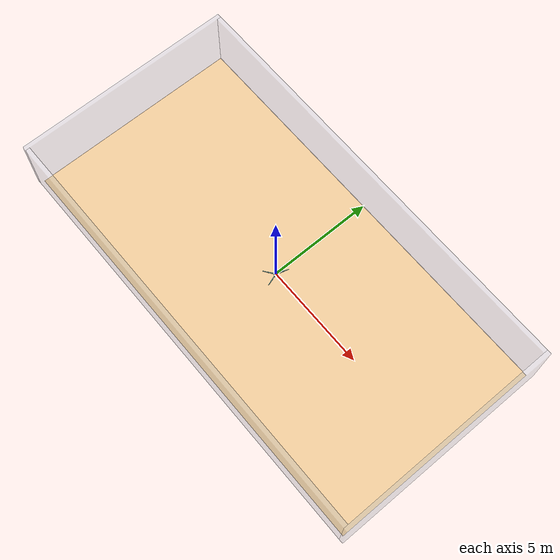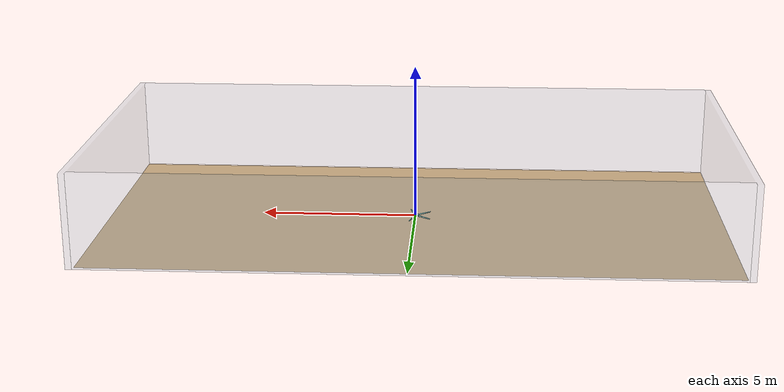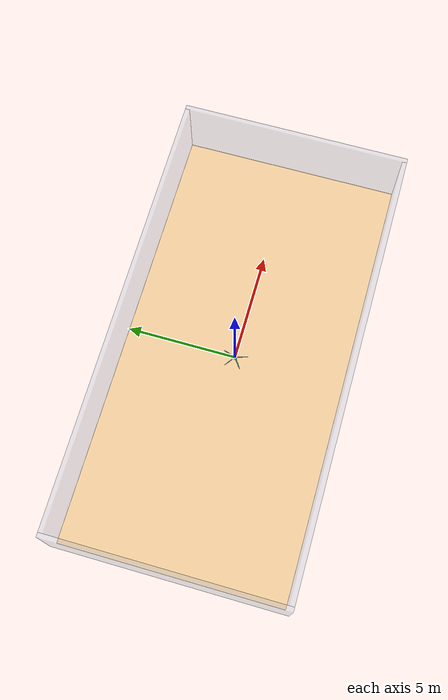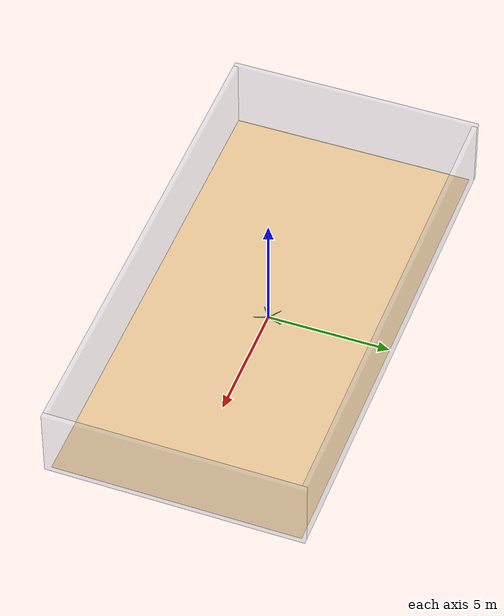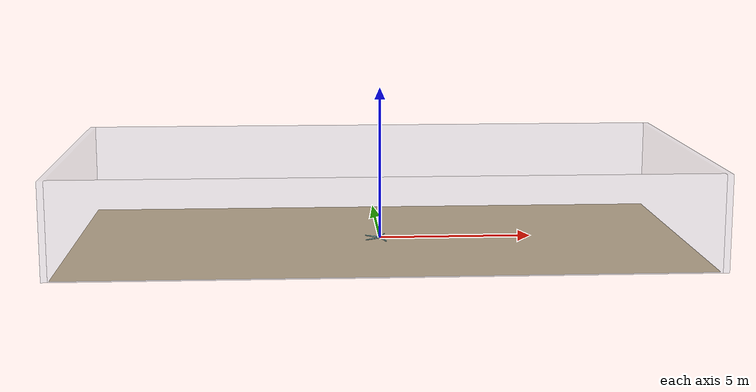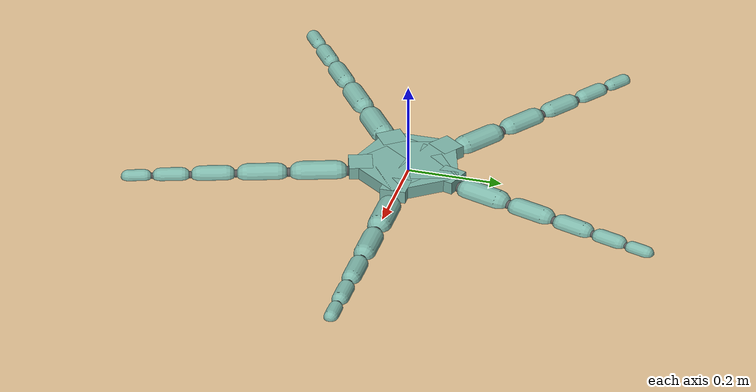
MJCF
<mujoco model="AquariumArena">
  <compiler angle="radian"/>
  <option density="1000" viscosity="0.00089999999999999998"/>
  <visual>
    <headlight ambient="0.40000000000000002 0.40000000000000002 0.40000000000000002" diffuse="0.80000000000000004 0.80000000000000004 0.80000000000000004" specular="0.10000000000000001 0.10000000000000001 0.10000000000000001"/>
  </visual>
  <default>
    <default class="/"/>
    <default class="BrittleStarMorphology/">
      <geom contype="1" conaffinity="0" condim="4" density="1100"/>
    </default>
  </default>
  <asset>
    <texture name="//unnamed_texture_0" type="skybox" builtin="flat" rgb1="1 1 1" rgb2="1 1 1" width="200" height="200"/>
    <texture name="groundplane" type="2d" builtin="flat" rgb1="0.88235294117647056 0.74901960784313726 0.5725490196078431" width="200" height="200"/>
    <material name="groundplane" class="/" texture="groundplane" reflectance="0"/>
  </asset>
  <worldbody>
    <camera name="top_camera" class="/" pos="0 0 20" quat="1 0 0 0"/>
    <light name="//unnamed_light_0" class="/" directional="true" castshadow="false" pos="-20 0 20" dir="0 0 -0.5" diffuse="0.10000000000000001 0.10000000000000001 0.10000000000000001"/>
    <geom name="groundplane" class="/" type="plane" contype="0" conaffinity="1" condim="4" size="10 5 0.25" material="groundplane" rgba="0.88235294117647056 0.74901960784313726 0.5725490196078431 1" friction="0.01 0.0001 0.0005"/>
    <geom name="north_wall" class="/" type="box" contype="0" conaffinity="0" size="10 0.10000000000000001 1.5" rgba="0.45098039215686275 0.57647058823529407 0.70196078431372544 0.19607843137254902" pos="0 5.0999999999999996 1.5"/>
    <geom name="south_wall" class="/" type="box" contype="0" conaffinity="0" size="10 0.10000000000000001 1.5" rgba="0.45098039215686275 0.57647058823529407 0.70196078431372544 0.19607843137254902" pos="0 -5.0999999999999996 1.5"/>
    <geom name="east_wall" class="/" type="box" contype="0" conaffinity="0" size="0.10000000000000001 5.2000000000000002 1.5" rgba="0.45098039215686275 0.57647058823529407 0.70196078431372544 0.19607843137254902" pos="-10.1 0 1.5"/>
    <geom name="west_wall" class="/" type="box" contype="0" conaffinity="0" size="0.10000000000000001 5.2000000000000002 1.5" rgba="0.45098039215686275 0.57647058823529407 0.70196078431372544 0.19607843137254902" pos="10.1 0 1.5"/>
    <geom name="north_wall_collider" class="/" type="plane" contype="0" conaffinity="1" size="10 0.10000000000000001 1.5" rgba="0 0 0 0" pos="0 5.0999999999999996 1.5" euler="1.5707963267948966 0 0"/>
    <geom name="south_wall_collider" class="/" type="plane" contype="0" conaffinity="1" size="10 0.10000000000000001 1.5" rgba="0 0 0 0" pos="0 -5.0999999999999996 1.5" euler="-1.5707963267948966 0 0"/>
    <geom name="east_wall_collider" class="/" type="plane" contype="0" conaffinity="1" size="0.10000000000000001 5.2000000000000002 1.5" rgba="0 0 0 0" pos="-10.1 0 1.5" euler="0 1.5707963267948966 0"/>
    <geom name="west_wall_collider" class="/" type="plane" contype="0" conaffinity="1" size="0.10000000000000001 5.2000000000000002 1.5" rgba="0 0 0 0" pos="10.1 0 1.5" euler="0 -1.5707963267948966 0"/>
    <site name="AquariumArena_attachment_BrittleStarMorphology" class="/"/>
    <body name="BrittleStarMorphology/">
      <freejoint name="BrittleStarMorphology/freejoint/"/>
      <body name="BrittleStarMorphology/central_disk" pos="0 0 0" euler="0 0 0">
        <geom name="BrittleStarMorphology/central_disk_pentagon_side_0" class="BrittleStarMorphology/" type="box" contype="0" conaffinity="0" size="0.050563562148434216 0.073473156536559142 0.025000000000000001" rgba="0.49019607843137253 0.70980392156862748 0.6588235294117647 1" mass="0" pos="0.040906781074217108 0.029720516134223551 0" euler="0 0 0.62831853071795862"/>
        <geom name="BrittleStarMorphology/central_disk_pentagon_side_1" class="BrittleStarMorphology/" type="box" contype="0" conaffinity="0" size="0.050563562148434216 0.073473156536559142 0.025000000000000001" rgba="0.49019607843137253 0.70980392156862748 0.6588235294117647 1" mass="0" pos="-0.015624999999999997 0.048088805268363337 0" euler="0 0 1.8849555921538759"/>
        <geom name="BrittleStarMorphology/central_disk_pentagon_side_2" class="BrittleStarMorphology/" type="box" contype="0" conaffinity="0" size="0.050563562148434216 0.073473156536559142 0.025000000000000001" rgba="0.49019607843137253 0.70980392156862748 0.6588235294117647 1" mass="0" pos="-0.050563562148434216 6.1922504538568225e-18 0" euler="0 0 3.1415926535897931"/>
        <geom name="BrittleStarMorphology/central_disk_pentagon_side_3" class="BrittleStarMorphology/" type="box" contype="0" conaffinity="0" size="0.050563562148434216 0.073473156536559142 0.025000000000000001" rgba="0.49019607843137253 0.70980392156862748 0.6588235294117647 1" mass="0" pos="-0.015625000000000007 -0.048088805268363337 0" euler="0 0 4.3982297150257104"/>
        <geom name="BrittleStarMorphology/central_disk_pentagon_side_4" class="BrittleStarMorphology/" type="box" contype="0" conaffinity="0" size="0.050563562148434216 0.073473156536559142 0.025000000000000001" rgba="0.49019607843137253 0.70980392156862748 0.6588235294117647 1" mass="0" pos="0.040906781074217101 -0.029720516134223562 0" euler="0 0 5.6548667764616276"/>
        <geom name="BrittleStarMorphology/central_disk_pentagon_collider" class="BrittleStarMorphology/" type="cylinder" contype="1" conaffinity="0" size="0.125 0.025000000000000001" rgba="0 0 0 0" pos="0 0 0" euler="0 0 0"/>
        <geom name="BrittleStarMorphology/central_disk_arm_connector_0" class="BrittleStarMorphology/" type="box" contype="0" conaffinity="0" size="0.025000000000000001 0.027500000000000004 0.025000000000000001" rgba="0.49019607843137253 0.70980392156862748 0.6588235294117647 1" pos="0.10000000000000001 0 0" euler="0 0 0"/>
        <geom name="BrittleStarMorphology/central_disk_arm_connector_1" class="BrittleStarMorphology/" type="box" contype="0" conaffinity="0" size="0.025000000000000001 0.027500000000000004 0.025000000000000001" rgba="0.49019607843137253 0.70980392156862748 0.6588235294117647 1" pos="0.030901699437494747 0.095105651629515356 0" euler="0 0 1.2566370614359172"/>
        <geom name="BrittleStarMorphology/central_disk_arm_connector_2" class="BrittleStarMorphology/" type="box" contype="0" conaffinity="0" size="0.025000000000000001 0.027500000000000004 0.025000000000000001" rgba="0.49019607843137253 0.70980392156862748 0.6588235294117647 1" pos="-0.080901699437494742 0.058778525229247328 0" euler="0 0 2.5132741228718345"/>
        <geom name="BrittleStarMorphology/central_disk_arm_connector_3" class="BrittleStarMorphology/" type="box" contype="0" conaffinity="0" size="0.025000000000000001 0.027500000000000004 0.025000000000000001" rgba="0.49019607843137253 0.70980392156862748 0.6588235294117647 1" pos="-0.080901699437494756 -0.058778525229247307 0" euler="0 0 3.7699111843077517"/>
        <geom name="BrittleStarMorphology/central_disk_arm_connector_4" class="BrittleStarMorphology/" type="box" contype="0" conaffinity="0" size="0.025000000000000001 0.027500000000000004 0.025000000000000001" rgba="0.49019607843137253 0.70980392156862748 0.6588235294117647 1" pos="0.030901699437494726 -0.09510565162951537 0" euler="0 0 5.026548245743669"/>
        <body name="BrittleStarMorphology/arm_0" pos="0.125 0 0" euler="0 0 0">
          <body name="BrittleStarMorphology/arm_0_segment_0" pos="0 0 0" euler="0 0 0">
            <geom name="BrittleStarMorphology/arm_0_segment_0_capsule" class="BrittleStarMorphology/" type="capsule" size="0.025000000000000001 0.037499999999999999" rgba="0.49019607843137253 0.70980392156862748 0.6588235294117647 1" pos="0.0625 0 0" euler="0 1.5707963267948966 0"/>
            <geom name="BrittleStarMorphology/arm_0_segment_0_connector" class="BrittleStarMorphology/" type="sphere" contype="0" conaffinity="0" size="0.012500000000000001" rgba="0.34901960784313724 0.34901960784313724 0.34901960784313724 1" pos="0 0 0"/>
            <joint name="BrittleStarMorphology/arm_0_segment_0_in_plane_joint" class="BrittleStarMorphology/" type="hinge" axis="0 0 1" limited="true" stiffness="0.01" range="-0.52359877559829882 0.52359877559829882" armature="0.02" damping="0.10000000000000001"/>
            <joint name="BrittleStarMorphology/arm_0_segment_0_out_of_plane_joint" class="BrittleStarMorphology/" type="hinge" axis="0 -1 0" limited="true" stiffness="0.01" range="-0.52359877559829882 0.52359877559829882" armature="0.02" damping="0.10000000000000001"/>
            <site name="BrittleStarMorphology/arm_0_segment_0_contact_site" class="BrittleStarMorphology/" type="capsule" rgba="0 0 0 0" size="0.025250000000000002 0.037874999999999999" pos="0.0625 0 0" euler="0 1.5707963267948966 0"/>
            <body name="BrittleStarMorphology/arm_0_segment_1" pos="0.125 0 0" euler="0 0 0">
              <geom name="BrittleStarMorphology/arm_0_segment_1_capsule" class="BrittleStarMorphology/" type="capsule" size="0.022499999999999999 0.032500000000000001" rgba="0.49019607843137253 0.70980392156862748 0.6588235294117647 1" pos="0.055 0 0" euler="0 1.5707963267948966 0"/>
              <geom name="BrittleStarMorphology/arm_0_segment_1_connector" class="BrittleStarMorphology/" type="sphere" contype="0" conaffinity="0" size="0.01125" rgba="0.34901960784313724 0.34901960784313724 0.34901960784313724 1" pos="0 0 0"/>
              <joint name="BrittleStarMorphology/arm_0_segment_1_in_plane_joint" class="BrittleStarMorphology/" type="hinge" axis="0 0 1" limited="true" stiffness="0.01" range="-0.52359877559829882 0.52359877559829882" armature="0.02" damping="0.10000000000000001"/>
              <joint name="BrittleStarMorphology/arm_0_segment_1_out_of_plane_joint" class="BrittleStarMorphology/" type="hinge" axis="0 -1 0" limited="true" stiffness="0.01" range="-0.52359877559829882 0.52359877559829882" armature="0.02" damping="0.10000000000000001"/>
              <site name="BrittleStarMorphology/arm_0_segment_1_contact_site" class="BrittleStarMorphology/" type="capsule" rgba="0 0 0 0" size="0.022724999999999999 0.032825" pos="0.055 0 0" euler="0 1.5707963267948966 0"/>
              <body name="BrittleStarMorphology/arm_0_segment_2" pos="0.11 0 0" euler="0 0 0">
                <geom name="BrittleStarMorphology/arm_0_segment_2_capsule" class="BrittleStarMorphology/" type="capsule" size="0.02 0.027499999999999997" rgba="0.49019607843137253 0.70980392156862748 0.6588235294117647 1" pos="0.047500000000000001 0 0" euler="0 1.5707963267948966 0"/>
                <geom name="BrittleStarMorphology/arm_0_segment_2_connector" class="BrittleStarMorphology/" type="sphere" contype="0" conaffinity="0" size="0.01" rgba="0.34901960784313724 0.34901960784313724 0.34901960784313724 1" pos="0 0 0"/>
                <joint name="BrittleStarMorphology/arm_0_segment_2_in_plane_joint" class="BrittleStarMorphology/" type="hinge" axis="0 0 1" limited="true" stiffness="0.01" range="-0.52359877559829882 0.52359877559829882" armature="0.02" damping="0.10000000000000001"/>
                <joint name="BrittleStarMorphology/arm_0_segment_2_out_of_plane_joint" class="BrittleStarMorphology/" type="hinge" axis="0 -1 0" limited="true" stiffness="0.01" range="-0.52359877559829882 0.52359877559829882" armature="0.02" damping="0.10000000000000001"/>
                <site name="BrittleStarMorphology/arm_0_segment_2_contact_site" class="BrittleStarMorphology/" type="capsule" rgba="0 0 0 0" size="0.020199999999999999 0.027774999999999998" pos="0.047500000000000001 0 0" euler="0 1.5707963267948966 0"/>
                <body name="BrittleStarMorphology/arm_0_segment_3" pos="0.095000000000000001 0 0" euler="0 0 0">
                  <geom name="BrittleStarMorphology/arm_0_segment_3_capsule" class="BrittleStarMorphology/" type="capsule" size="0.017500000000000002 0.022499999999999999" rgba="0.49019607843137253 0.70980392156862748 0.6588235294117647 1" pos="0.040000000000000001 0 0" euler="0 1.5707963267948966 0"/>
                  <geom name="BrittleStarMorphology/arm_0_segment_3_connector" class="BrittleStarMorphology/" type="sphere" contype="0" conaffinity="0" size="0.0087500000000000008" rgba="0.34901960784313724 0.34901960784313724 0.34901960784313724 1" pos="0 0 0"/>
                  <joint name="BrittleStarMorphology/arm_0_segment_3_in_plane_joint" class="BrittleStarMorphology/" type="hinge" axis="0 0 1" limited="true" stiffness="0.01" range="-0.52359877559829882 0.52359877559829882" armature="0.02" damping="0.10000000000000001"/>
                  <joint name="BrittleStarMorphology/arm_0_segment_3_out_of_plane_joint" class="BrittleStarMorphology/" type="hinge" axis="0 -1 0" limited="true" stiffness="0.01" range="-0.52359877559829882 0.52359877559829882" armature="0.02" damping="0.10000000000000001"/>
                  <site name="BrittleStarMorphology/arm_0_segment_3_contact_site" class="BrittleStarMorphology/" type="capsule" rgba="0 0 0 0" size="0.017675000000000003 0.022724999999999999" pos="0.040000000000000001 0 0" euler="0 1.5707963267948966 0"/>
                  <body name="BrittleStarMorphology/arm_0_segment_4" pos="0.080000000000000002 0 0" euler="0 0 0">
                    <geom name="BrittleStarMorphology/arm_0_segment_4_capsule" class="BrittleStarMorphology/" type="capsule" size="0.014999999999999999 0.017499999999999998" rgba="0.49019607843137253 0.70980392156862748 0.6588235294117647 1" pos="0.032500000000000001 0 0" euler="0 1.5707963267948966 0"/>
                    <geom name="BrittleStarMorphology/arm_0_segment_4_connector" class="BrittleStarMorphology/" type="sphere" contype="0" conaffinity="0" size="0.0074999999999999997" rgba="0.34901960784313724 0.34901960784313724 0.34901960784313724 1" pos="0 0 0"/>
                    <joint name="BrittleStarMorphology/arm_0_segment_4_in_plane_joint" class="BrittleStarMorphology/" type="hinge" axis="0 0 1" limited="true" stiffness="0.01" range="-0.52359877559829882 0.52359877559829882" armature="0.02" damping="0.10000000000000001"/>
                    <joint name="BrittleStarMorphology/arm_0_segment_4_out_of_plane_joint" class="BrittleStarMorphology/" type="hinge" axis="0 -1 0" limited="true" stiffness="0.01" range="-0.52359877559829882 0.52359877559829882" armature="0.02" damping="0.10000000000000001"/>
                    <site name="BrittleStarMorphology/arm_0_segment_4_contact_site" class="BrittleStarMorphology/" type="capsule" rgba="0 0 0 0" size="0.01515 0.017675" pos="0.032500000000000001 0 0" euler="0 1.5707963267948966 0"/>
                  </body>
                </body>
              </body>
            </body>
          </body>
        </body>
        <body name="BrittleStarMorphology/arm_1" pos="0.038627124296868431 0.11888206453689419 0" euler="0 0 1.2566370614359172">
          <body name="BrittleStarMorphology/arm_1_segment_0" pos="0 0 0" euler="0 0 0">
            <geom name="BrittleStarMorphology/arm_1_segment_0_capsule" class="BrittleStarMorphology/" type="capsule" size="0.025000000000000001 0.037499999999999999" rgba="0.49019607843137253 0.70980392156862748 0.6588235294117647 1" pos="0.0625 0 0" euler="0 1.5707963267948966 0"/>
            <geom name="BrittleStarMorphology/arm_1_segment_0_connector" class="BrittleStarMorphology/" type="sphere" contype="0" conaffinity="0" size="0.012500000000000001" rgba="0.34901960784313724 0.34901960784313724 0.34901960784313724 1" pos="0 0 0"/>
            <joint name="BrittleStarMorphology/arm_1_segment_0_in_plane_joint" class="BrittleStarMorphology/" type="hinge" axis="0 0 1" limited="true" stiffness="0.01" range="-0.52359877559829882 0.52359877559829882" armature="0.02" damping="0.10000000000000001"/>
            <joint name="BrittleStarMorphology/arm_1_segment_0_out_of_plane_joint" class="BrittleStarMorphology/" type="hinge" axis="0 -1 0" limited="true" stiffness="0.01" range="-0.52359877559829882 0.52359877559829882" armature="0.02" damping="0.10000000000000001"/>
            <site name="BrittleStarMorphology/arm_1_segment_0_contact_site" class="BrittleStarMorphology/" type="capsule" rgba="0 0 0 0" size="0.025250000000000002 0.037874999999999999" pos="0.0625 0 0" euler="0 1.5707963267948966 0"/>
            <body name="BrittleStarMorphology/arm_1_segment_1" pos="0.125 0 0" euler="0 0 0">
              <geom name="BrittleStarMorphology/arm_1_segment_1_capsule" class="BrittleStarMorphology/" type="capsule" size="0.022499999999999999 0.032500000000000001" rgba="0.49019607843137253 0.70980392156862748 0.6588235294117647 1" pos="0.055 0 0" euler="0 1.5707963267948966 0"/>
              <geom name="BrittleStarMorphology/arm_1_segment_1_connector" class="BrittleStarMorphology/" type="sphere" contype="0" conaffinity="0" size="0.01125" rgba="0.34901960784313724 0.34901960784313724 0.34901960784313724 1" pos="0 0 0"/>
              <joint name="BrittleStarMorphology/arm_1_segment_1_in_plane_joint" class="BrittleStarMorphology/" type="hinge" axis="0 0 1" limited="true" stiffness="0.01" range="-0.52359877559829882 0.52359877559829882" armature="0.02" damping="0.10000000000000001"/>
              <joint name="BrittleStarMorphology/arm_1_segment_1_out_of_plane_joint" class="BrittleStarMorphology/" type="hinge" axis="0 -1 0" limited="true" stiffness="0.01" range="-0.52359877559829882 0.52359877559829882" armature="0.02" damping="0.10000000000000001"/>
              <site name="BrittleStarMorphology/arm_1_segment_1_contact_site" class="BrittleStarMorphology/" type="capsule" rgba="0 0 0 0" size="0.022724999999999999 0.032825" pos="0.055 0 0" euler="0 1.5707963267948966 0"/>
              <body name="BrittleStarMorphology/arm_1_segment_2" pos="0.11 0 0" euler="0 0 0">
                <geom name="BrittleStarMorphology/arm_1_segment_2_capsule" class="BrittleStarMorphology/" type="capsule" size="0.02 0.027499999999999997" rgba="0.49019607843137253 0.70980392156862748 0.6588235294117647 1" pos="0.047500000000000001 0 0" euler="0 1.5707963267948966 0"/>
                <geom name="BrittleStarMorphology/arm_1_segment_2_connector" class="BrittleStarMorphology/" type="sphere" contype="0" conaffinity="0" size="0.01" rgba="0.34901960784313724 0.34901960784313724 0.34901960784313724 1" pos="0 0 0"/>
                <joint name="BrittleStarMorphology/arm_1_segment_2_in_plane_joint" class="BrittleStarMorphology/" type="hinge" axis="0 0 1" limited="true" stiffness="0.01" range="-0.52359877559829882 0.52359877559829882" armature="0.02" damping="0.10000000000000001"/>
                <joint name="BrittleStarMorphology/arm_1_segment_2_out_of_plane_joint" class="BrittleStarMorphology/" type="hinge" axis="0 -1 0" limited="true" stiffness="0.01" range="-0.52359877559829882 0.52359877559829882" armature="0.02" damping="0.10000000000000001"/>
                <site name="BrittleStarMorphology/arm_1_segment_2_contact_site" class="BrittleStarMorphology/" type="capsule" rgba="0 0 0 0" size="0.020199999999999999 0.027774999999999998" pos="0.047500000000000001 0 0" euler="0 1.5707963267948966 0"/>
                <body name="BrittleStarMorphology/arm_1_segment_3" pos="0.095000000000000001 0 0" euler="0 0 0">
                  <geom name="BrittleStarMorphology/arm_1_segment_3_capsule" class="BrittleStarMorphology/" type="capsule" size="0.017500000000000002 0.022499999999999999" rgba="0.49019607843137253 0.70980392156862748 0.6588235294117647 1" pos="0.040000000000000001 0 0" euler="0 1.5707963267948966 0"/>
                  <geom name="BrittleStarMorphology/arm_1_segment_3_connector" class="BrittleStarMorphology/" type="sphere" contype="0" conaffinity="0" size="0.0087500000000000008" rgba="0.34901960784313724 0.34901960784313724 0.34901960784313724 1" pos="0 0 0"/>
                  <joint name="BrittleStarMorphology/arm_1_segment_3_in_plane_joint" class="BrittleStarMorphology/" type="hinge" axis="0 0 1" limited="true" stiffness="0.01" range="-0.52359877559829882 0.52359877559829882" armature="0.02" damping="0.10000000000000001"/>
                  <joint name="BrittleStarMorphology/arm_1_segment_3_out_of_plane_joint" class="BrittleStarMorphology/" type="hinge" axis="0 -1 0" limited="true" stiffness="0.01" range="-0.52359877559829882 0.52359877559829882" armature="0.02" damping="0.10000000000000001"/>
                  <site name="BrittleStarMorphology/arm_1_segment_3_contact_site" class="BrittleStarMorphology/" type="capsule" rgba="0 0 0 0" size="0.017675000000000003 0.022724999999999999" pos="0.040000000000000001 0 0" euler="0 1.5707963267948966 0"/>
                  <body name="BrittleStarMorphology/arm_1_segment_4" pos="0.080000000000000002 0 0" euler="0 0 0">
                    <geom name="BrittleStarMorphology/arm_1_segment_4_capsule" class="BrittleStarMorphology/" type="capsule" size="0.014999999999999999 0.017499999999999998" rgba="0.49019607843137253 0.70980392156862748 0.6588235294117647 1" pos="0.032500000000000001 0 0" euler="0 1.5707963267948966 0"/>
                    <geom name="BrittleStarMorphology/arm_1_segment_4_connector" class="BrittleStarMorphology/" type="sphere" contype="0" conaffinity="0" size="0.0074999999999999997" rgba="0.34901960784313724 0.34901960784313724 0.34901960784313724 1" pos="0 0 0"/>
                    <joint name="BrittleStarMorphology/arm_1_segment_4_in_plane_joint" class="BrittleStarMorphology/" type="hinge" axis="0 0 1" limited="true" stiffness="0.01" range="-0.52359877559829882 0.52359877559829882" armature="0.02" damping="0.10000000000000001"/>
                    <joint name="BrittleStarMorphology/arm_1_segment_4_out_of_plane_joint" class="BrittleStarMorphology/" type="hinge" axis="0 -1 0" limited="true" stiffness="0.01" range="-0.52359877559829882 0.52359877559829882" armature="0.02" damping="0.10000000000000001"/>
                    <site name="BrittleStarMorphology/arm_1_segment_4_contact_site" class="BrittleStarMorphology/" type="capsule" rgba="0 0 0 0" size="0.01515 0.017675" pos="0.032500000000000001 0 0" euler="0 1.5707963267948966 0"/>
                  </body>
                </body>
              </body>
            </body>
          </body>
        </body>
        <body name="BrittleStarMorphology/arm_2" pos="-0.10112712429686842 0.073473156536559156 0" euler="0 0 2.5132741228718345">
          <body name="BrittleStarMorphology/arm_2_segment_0" pos="0 0 0" euler="0 0 0">
            <geom name="BrittleStarMorphology/arm_2_segment_0_capsule" class="BrittleStarMorphology/" type="capsule" size="0.025000000000000001 0.037499999999999999" rgba="0.49019607843137253 0.70980392156862748 0.6588235294117647 1" pos="0.0625 0 0" euler="0 1.5707963267948966 0"/>
            <geom name="BrittleStarMorphology/arm_2_segment_0_connector" class="BrittleStarMorphology/" type="sphere" contype="0" conaffinity="0" size="0.012500000000000001" rgba="0.34901960784313724 0.34901960784313724 0.34901960784313724 1" pos="0 0 0"/>
            <joint name="BrittleStarMorphology/arm_2_segment_0_in_plane_joint" class="BrittleStarMorphology/" type="hinge" axis="0 0 1" limited="true" stiffness="0.01" range="-0.52359877559829882 0.52359877559829882" armature="0.02" damping="0.10000000000000001"/>
            <joint name="BrittleStarMorphology/arm_2_segment_0_out_of_plane_joint" class="BrittleStarMorphology/" type="hinge" axis="0 -1 0" limited="true" stiffness="0.01" range="-0.52359877559829882 0.52359877559829882" armature="0.02" damping="0.10000000000000001"/>
            <site name="BrittleStarMorphology/arm_2_segment_0_contact_site" class="BrittleStarMorphology/" type="capsule" rgba="0 0 0 0" size="0.025250000000000002 0.037874999999999999" pos="0.0625 0 0" euler="0 1.5707963267948966 0"/>
            <body name="BrittleStarMorphology/arm_2_segment_1" pos="0.125 0 0" euler="0 0 0">
              <geom name="BrittleStarMorphology/arm_2_segment_1_capsule" class="BrittleStarMorphology/" type="capsule" size="0.022499999999999999 0.032500000000000001" rgba="0.49019607843137253 0.70980392156862748 0.6588235294117647 1" pos="0.055 0 0" euler="0 1.5707963267948966 0"/>
              <geom name="BrittleStarMorphology/arm_2_segment_1_connector" class="BrittleStarMorphology/" type="sphere" contype="0" conaffinity="0" size="0.01125" rgba="0.34901960784313724 0.34901960784313724 0.34901960784313724 1" pos="0 0 0"/>
              <joint name="BrittleStarMorphology/arm_2_segment_1_in_plane_joint" class="BrittleStarMorphology/" type="hinge" axis="0 0 1" limited="true" stiffness="0.01" range="-0.52359877559829882 0.52359877559829882" armature="0.02" damping="0.10000000000000001"/>
              <joint name="BrittleStarMorphology/arm_2_segment_1_out_of_plane_joint" class="BrittleStarMorphology/" type="hinge" axis="0 -1 0" limited="true" stiffness="0.01" range="-0.52359877559829882 0.52359877559829882" armature="0.02" damping="0.10000000000000001"/>
              <site name="BrittleStarMorphology/arm_2_segment_1_contact_site" class="BrittleStarMorphology/" type="capsule" rgba="0 0 0 0" size="0.022724999999999999 0.032825" pos="0.055 0 0" euler="0 1.5707963267948966 0"/>
              <body name="BrittleStarMorphology/arm_2_segment_2" pos="0.11 0 0" euler="0 0 0">
                <geom name="BrittleStarMorphology/arm_2_segment_2_capsule" class="BrittleStarMorphology/" type="capsule" size="0.02 0.027499999999999997" rgba="0.49019607843137253 0.70980392156862748 0.6588235294117647 1" pos="0.047500000000000001 0 0" euler="0 1.5707963267948966 0"/>
                <geom name="BrittleStarMorphology/arm_2_segment_2_connector" class="BrittleStarMorphology/" type="sphere" contype="0" conaffinity="0" size="0.01" rgba="0.34901960784313724 0.34901960784313724 0.34901960784313724 1" pos="0 0 0"/>
                <joint name="BrittleStarMorphology/arm_2_segment_2_in_plane_joint" class="BrittleStarMorphology/" type="hinge" axis="0 0 1" limited="true" stiffness="0.01" range="-0.52359877559829882 0.52359877559829882" armature="0.02" damping="0.10000000000000001"/>
                <joint name="BrittleStarMorphology/arm_2_segment_2_out_of_plane_joint" class="BrittleStarMorphology/" type="hinge" axis="0 -1 0" limited="true" stiffness="0.01" range="-0.52359877559829882 0.52359877559829882" armature="0.02" damping="0.10000000000000001"/>
                <site name="BrittleStarMorphology/arm_2_segment_2_contact_site" class="BrittleStarMorphology/" type="capsule" rgba="0 0 0 0" size="0.020199999999999999 0.027774999999999998" pos="0.047500000000000001 0 0" euler="0 1.5707963267948966 0"/>
                <body name="BrittleStarMorphology/arm_2_segment_3" pos="0.095000000000000001 0 0" euler="0 0 0">
                  <geom name="BrittleStarMorphology/arm_2_segment_3_capsule" class="BrittleStarMorphology/" type="capsule" size="0.017500000000000002 0.022499999999999999" rgba="0.49019607843137253 0.70980392156862748 0.6588235294117647 1" pos="0.040000000000000001 0 0" euler="0 1.5707963267948966 0"/>
                  <geom name="BrittleStarMorphology/arm_2_segment_3_connector" class="BrittleStarMorphology/" type="sphere" contype="0" conaffinity="0" size="0.0087500000000000008" rgba="0.34901960784313724 0.34901960784313724 0.34901960784313724 1" pos="0 0 0"/>
                  <joint name="BrittleStarMorphology/arm_2_segment_3_in_plane_joint" class="BrittleStarMorphology/" type="hinge" axis="0 0 1" limited="true" stiffness="0.01" range="-0.52359877559829882 0.52359877559829882" armature="0.02" damping="0.10000000000000001"/>
                  <joint name="BrittleStarMorphology/arm_2_segment_3_out_of_plane_joint" class="BrittleStarMorphology/" type="hinge" axis="0 -1 0" limited="true" stiffness="0.01" range="-0.52359877559829882 0.52359877559829882" armature="0.02" damping="0.10000000000000001"/>
                  <site name="BrittleStarMorphology/arm_2_segment_3_contact_site" class="BrittleStarMorphology/" type="capsule" rgba="0 0 0 0" size="0.017675000000000003 0.022724999999999999" pos="0.040000000000000001 0 0" euler="0 1.5707963267948966 0"/>
                  <body name="BrittleStarMorphology/arm_2_segment_4" pos="0.080000000000000002 0 0" euler="0 0 0">
                    <geom name="BrittleStarMorphology/arm_2_segment_4_capsule" class="BrittleStarMorphology/" type="capsule" size="0.014999999999999999 0.017499999999999998" rgba="0.49019607843137253 0.70980392156862748 0.6588235294117647 1" pos="0.032500000000000001 0 0" euler="0 1.5707963267948966 0"/>
                    <geom name="BrittleStarMorphology/arm_2_segment_4_connector" class="BrittleStarMorphology/" type="sphere" contype="0" conaffinity="0" size="0.0074999999999999997" rgba="0.34901960784313724 0.34901960784313724 0.34901960784313724 1" pos="0 0 0"/>
                    <joint name="BrittleStarMorphology/arm_2_segment_4_in_plane_joint" class="BrittleStarMorphology/" type="hinge" axis="0 0 1" limited="true" stiffness="0.01" range="-0.52359877559829882 0.52359877559829882" armature="0.02" damping="0.10000000000000001"/>
                    <joint name="BrittleStarMorphology/arm_2_segment_4_out_of_plane_joint" class="BrittleStarMorphology/" type="hinge" axis="0 -1 0" limited="true" stiffness="0.01" range="-0.52359877559829882 0.52359877559829882" armature="0.02" damping="0.10000000000000001"/>
                    <site name="BrittleStarMorphology/arm_2_segment_4_contact_site" class="BrittleStarMorphology/" type="capsule" rgba="0 0 0 0" size="0.01515 0.017675" pos="0.032500000000000001 0 0" euler="0 1.5707963267948966 0"/>
                  </body>
                </body>
              </body>
            </body>
          </body>
        </body>
        <body name="BrittleStarMorphology/arm_3" pos="-0.10112712429686843 -0.073473156536559128 0" euler="0 0 3.7699111843077517">
          <body name="BrittleStarMorphology/arm_3_segment_0" pos="0 0 0" euler="0 0 0">
            <geom name="BrittleStarMorphology/arm_3_segment_0_capsule" class="BrittleStarMorphology/" type="capsule" size="0.025000000000000001 0.037499999999999999" rgba="0.49019607843137253 0.70980392156862748 0.6588235294117647 1" pos="0.0625 0 0" euler="0 1.5707963267948966 0"/>
            <geom name="BrittleStarMorphology/arm_3_segment_0_connector" class="BrittleStarMorphology/" type="sphere" contype="0" conaffinity="0" size="0.012500000000000001" rgba="0.34901960784313724 0.34901960784313724 0.34901960784313724 1" pos="0 0 0"/>
            <joint name="BrittleStarMorphology/arm_3_segment_0_in_plane_joint" class="BrittleStarMorphology/" type="hinge" axis="0 0 1" limited="true" stiffness="0.01" range="-0.52359877559829882 0.52359877559829882" armature="0.02" damping="0.10000000000000001"/>
            <joint name="BrittleStarMorphology/arm_3_segment_0_out_of_plane_joint" class="BrittleStarMorphology/" type="hinge" axis="0 -1 0" limited="true" stiffness="0.01" range="-0.52359877559829882 0.52359877559829882" armature="0.02" damping="0.10000000000000001"/>
            <site name="BrittleStarMorphology/arm_3_segment_0_contact_site" class="BrittleStarMorphology/" type="capsule" rgba="0 0 0 0" size="0.025250000000000002 0.037874999999999999" pos="0.0625 0 0" euler="0 1.5707963267948966 0"/>
            <body name="BrittleStarMorphology/arm_3_segment_1" pos="0.125 0 0" euler="0 0 0">
              <geom name="BrittleStarMorphology/arm_3_segment_1_capsule" class="BrittleStarMorphology/" type="capsule" size="0.022499999999999999 0.032500000000000001" rgba="0.49019607843137253 0.70980392156862748 0.6588235294117647 1" pos="0.055 0 0" euler="0 1.5707963267948966 0"/>
              <geom name="BrittleStarMorphology/arm_3_segment_1_connector" class="BrittleStarMorphology/" type="sphere" contype="0" conaffinity="0" size="0.01125" rgba="0.34901960784313724 0.34901960784313724 0.34901960784313724 1" pos="0 0 0"/>
              <joint name="BrittleStarMorphology/arm_3_segment_1_in_plane_joint" class="BrittleStarMorphology/" type="hinge" axis="0 0 1" limited="true" stiffness="0.01" range="-0.52359877559829882 0.52359877559829882" armature="0.02" damping="0.10000000000000001"/>
              <joint name="BrittleStarMorphology/arm_3_segment_1_out_of_plane_joint" class="BrittleStarMorphology/" type="hinge" axis="0 -1 0" limited="true" stiffness="0.01" range="-0.52359877559829882 0.52359877559829882" armature="0.02" damping="0.10000000000000001"/>
              <site name="BrittleStarMorphology/arm_3_segment_1_contact_site" class="BrittleStarMorphology/" type="capsule" rgba="0 0 0 0" size="0.022724999999999999 0.032825" pos="0.055 0 0" euler="0 1.5707963267948966 0"/>
              <body name="BrittleStarMorphology/arm_3_segment_2" pos="0.11 0 0" euler="0 0 0">
                <geom name="BrittleStarMorphology/arm_3_segment_2_capsule" class="BrittleStarMorphology/" type="capsule" size="0.02 0.027499999999999997" rgba="0.49019607843137253 0.70980392156862748 0.6588235294117647 1" pos="0.047500000000000001 0 0" euler="0 1.5707963267948966 0"/>
                <geom name="BrittleStarMorphology/arm_3_segment_2_connector" class="BrittleStarMorphology/" type="sphere" contype="0" conaffinity="0" size="0.01" rgba="0.34901960784313724 0.34901960784313724 0.34901960784313724 1" pos="0 0 0"/>
                <joint name="BrittleStarMorphology/arm_3_segment_2_in_plane_joint" class="BrittleStarMorphology/" type="hinge" axis="0 0 1" limited="true" stiffness="0.01" range="-0.52359877559829882 0.52359877559829882" armature="0.02" damping="0.10000000000000001"/>
                <joint name="BrittleStarMorphology/arm_3_segment_2_out_of_plane_joint" class="BrittleStarMorphology/" type="hinge" axis="0 -1 0" limited="true" stiffness="0.01" range="-0.52359877559829882 0.52359877559829882" armature="0.02" damping="0.10000000000000001"/>
                <site name="BrittleStarMorphology/arm_3_segment_2_contact_site" class="BrittleStarMorphology/" type="capsule" rgba="0 0 0 0" size="0.020199999999999999 0.027774999999999998" pos="0.047500000000000001 0 0" euler="0 1.5707963267948966 0"/>
                <body name="BrittleStarMorphology/arm_3_segment_3" pos="0.095000000000000001 0 0" euler="0 0 0">
                  <geom name="BrittleStarMorphology/arm_3_segment_3_capsule" class="BrittleStarMorphology/" type="capsule" size="0.017500000000000002 0.022499999999999999" rgba="0.49019607843137253 0.70980392156862748 0.6588235294117647 1" pos="0.040000000000000001 0 0" euler="0 1.5707963267948966 0"/>
                  <geom name="BrittleStarMorphology/arm_3_segment_3_connector" class="BrittleStarMorphology/" type="sphere" contype="0" conaffinity="0" size="0.0087500000000000008" rgba="0.34901960784313724 0.34901960784313724 0.34901960784313724 1" pos="0 0 0"/>
                  <joint name="BrittleStarMorphology/arm_3_segment_3_in_plane_joint" class="BrittleStarMorphology/" type="hinge" axis="0 0 1" limited="true" stiffness="0.01" range="-0.52359877559829882 0.52359877559829882" armature="0.02" damping="0.10000000000000001"/>
                  <joint name="BrittleStarMorphology/arm_3_segment_3_out_of_plane_joint" class="BrittleStarMorphology/" type="hinge" axis="0 -1 0" limited="true" stiffness="0.01" range="-0.52359877559829882 0.52359877559829882" armature="0.02" damping="0.10000000000000001"/>
                  <site name="BrittleStarMorphology/arm_3_segment_3_contact_site" class="BrittleStarMorphology/" type="capsule" rgba="0 0 0 0" size="0.017675000000000003 0.022724999999999999" pos="0.040000000000000001 0 0" euler="0 1.5707963267948966 0"/>
                  <body name="BrittleStarMorphology/arm_3_segment_4" pos="0.080000000000000002 0 0" euler="0 0 0">
                    <geom name="BrittleStarMorphology/arm_3_segment_4_capsule" class="BrittleStarMorphology/" type="capsule" size="0.014999999999999999 0.017499999999999998" rgba="0.49019607843137253 0.70980392156862748 0.6588235294117647 1" pos="0.032500000000000001 0 0" euler="0 1.5707963267948966 0"/>
                    <geom name="BrittleStarMorphology/arm_3_segment_4_connector" class="BrittleStarMorphology/" type="sphere" contype="0" conaffinity="0" size="0.0074999999999999997" rgba="0.34901960784313724 0.34901960784313724 0.34901960784313724 1" pos="0 0 0"/>
                    <joint name="BrittleStarMorphology/arm_3_segment_4_in_plane_joint" class="BrittleStarMorphology/" type="hinge" axis="0 0 1" limited="true" stiffness="0.01" range="-0.52359877559829882 0.52359877559829882" armature="0.02" damping="0.10000000000000001"/>
                    <joint name="BrittleStarMorphology/arm_3_segment_4_out_of_plane_joint" class="BrittleStarMorphology/" type="hinge" axis="0 -1 0" limited="true" stiffness="0.01" range="-0.52359877559829882 0.52359877559829882" armature="0.02" damping="0.10000000000000001"/>
                    <site name="BrittleStarMorphology/arm_3_segment_4_contact_site" class="BrittleStarMorphology/" type="capsule" rgba="0 0 0 0" size="0.01515 0.017675" pos="0.032500000000000001 0 0" euler="0 1.5707963267948966 0"/>
                  </body>
                </body>
              </body>
            </body>
          </body>
        </body>
        <body name="BrittleStarMorphology/arm_4" pos="0.038627124296868404 -0.11888206453689421 0" euler="0 0 5.026548245743669">
          <body name="BrittleStarMorphology/arm_4_segment_0" pos="0 0 0" euler="0 0 0">
            <geom name="BrittleStarMorphology/arm_4_segment_0_capsule" class="BrittleStarMorphology/" type="capsule" size="0.025000000000000001 0.037499999999999999" rgba="0.49019607843137253 0.70980392156862748 0.6588235294117647 1" pos="0.0625 0 0" euler="0 1.5707963267948966 0"/>
            <geom name="BrittleStarMorphology/arm_4_segment_0_connector" class="BrittleStarMorphology/" type="sphere" contype="0" conaffinity="0" size="0.012500000000000001" rgba="0.34901960784313724 0.34901960784313724 0.34901960784313724 1" pos="0 0 0"/>
            <joint name="BrittleStarMorphology/arm_4_segment_0_in_plane_joint" class="BrittleStarMorphology/" type="hinge" axis="0 0 1" limited="true" stiffness="0.01" range="-0.52359877559829882 0.52359877559829882" armature="0.02" damping="0.10000000000000001"/>
            <joint name="BrittleStarMorphology/arm_4_segment_0_out_of_plane_joint" class="BrittleStarMorphology/" type="hinge" axis="0 -1 0" limited="true" stiffness="0.01" range="-0.52359877559829882 0.52359877559829882" armature="0.02" damping="0.10000000000000001"/>
            <site name="BrittleStarMorphology/arm_4_segment_0_contact_site" class="BrittleStarMorphology/" type="capsule" rgba="0 0 0 0" size="0.025250000000000002 0.037874999999999999" pos="0.0625 0 0" euler="0 1.5707963267948966 0"/>
            <body name="BrittleStarMorphology/arm_4_segment_1" pos="0.125 0 0" euler="0 0 0">
              <geom name="BrittleStarMorphology/arm_4_segment_1_capsule" class="BrittleStarMorphology/" type="capsule" size="0.022499999999999999 0.032500000000000001" rgba="0.49019607843137253 0.70980392156862748 0.6588235294117647 1" pos="0.055 0 0" euler="0 1.5707963267948966 0"/>
              <geom name="BrittleStarMorphology/arm_4_segment_1_connector" class="BrittleStarMorphology/" type="sphere" contype="0" conaffinity="0" size="0.01125" rgba="0.34901960784313724 0.34901960784313724 0.34901960784313724 1" pos="0 0 0"/>
              <joint name="BrittleStarMorphology/arm_4_segment_1_in_plane_joint" class="BrittleStarMorphology/" type="hinge" axis="0 0 1" limited="true" stiffness="0.01" range="-0.52359877559829882 0.52359877559829882" armature="0.02" damping="0.10000000000000001"/>
              <joint name="BrittleStarMorphology/arm_4_segment_1_out_of_plane_joint" class="BrittleStarMorphology/" type="hinge" axis="0 -1 0" limited="true" stiffness="0.01" range="-0.52359877559829882 0.52359877559829882" armature="0.02" damping="0.10000000000000001"/>
              <site name="BrittleStarMorphology/arm_4_segment_1_contact_site" class="BrittleStarMorphology/" type="capsule" rgba="0 0 0 0" size="0.022724999999999999 0.032825" pos="0.055 0 0" euler="0 1.5707963267948966 0"/>
              <body name="BrittleStarMorphology/arm_4_segment_2" pos="0.11 0 0" euler="0 0 0">
                <geom name="BrittleStarMorphology/arm_4_segment_2_capsule" class="BrittleStarMorphology/" type="capsule" size="0.02 0.027499999999999997" rgba="0.49019607843137253 0.70980392156862748 0.6588235294117647 1" pos="0.047500000000000001 0 0" euler="0 1.5707963267948966 0"/>
                <geom name="BrittleStarMorphology/arm_4_segment_2_connector" class="BrittleStarMorphology/" type="sphere" contype="0" conaffinity="0" size="0.01" rgba="0.34901960784313724 0.34901960784313724 0.34901960784313724 1" pos="0 0 0"/>
                <joint name="BrittleStarMorphology/arm_4_segment_2_in_plane_joint" class="BrittleStarMorphology/" type="hinge" axis="0 0 1" limited="true" stiffness="0.01" range="-0.52359877559829882 0.52359877559829882" armature="0.02" damping="0.10000000000000001"/>
                <joint name="BrittleStarMorphology/arm_4_segment_2_out_of_plane_joint" class="BrittleStarMorphology/" type="hinge" axis="0 -1 0" limited="true" stiffness="0.01" range="-0.52359877559829882 0.52359877559829882" armature="0.02" damping="0.10000000000000001"/>
                <site name="BrittleStarMorphology/arm_4_segment_2_contact_site" class="BrittleStarMorphology/" type="capsule" rgba="0 0 0 0" size="0.020199999999999999 0.027774999999999998" pos="0.047500000000000001 0 0" euler="0 1.5707963267948966 0"/>
                <body name="BrittleStarMorphology/arm_4_segment_3" pos="0.095000000000000001 0 0" euler="0 0 0">
                  <geom name="BrittleStarMorphology/arm_4_segment_3_capsule" class="BrittleStarMorphology/" type="capsule" size="0.017500000000000002 0.022499999999999999" rgba="0.49019607843137253 0.70980392156862748 0.6588235294117647 1" pos="0.040000000000000001 0 0" euler="0 1.5707963267948966 0"/>
                  <geom name="BrittleStarMorphology/arm_4_segment_3_connector" class="BrittleStarMorphology/" type="sphere" contype="0" conaffinity="0" size="0.0087500000000000008" rgba="0.34901960784313724 0.34901960784313724 0.34901960784313724 1" pos="0 0 0"/>
                  <joint name="BrittleStarMorphology/arm_4_segment_3_in_plane_joint" class="BrittleStarMorphology/" type="hinge" axis="0 0 1" limited="true" stiffness="0.01" range="-0.52359877559829882 0.52359877559829882" armature="0.02" damping="0.10000000000000001"/>
                  <joint name="BrittleStarMorphology/arm_4_segment_3_out_of_plane_joint" class="BrittleStarMorphology/" type="hinge" axis="0 -1 0" limited="true" stiffness="0.01" range="-0.52359877559829882 0.52359877559829882" armature="0.02" damping="0.10000000000000001"/>
                  <site name="BrittleStarMorphology/arm_4_segment_3_contact_site" class="BrittleStarMorphology/" type="capsule" rgba="0 0 0 0" size="0.017675000000000003 0.022724999999999999" pos="0.040000000000000001 0 0" euler="0 1.5707963267948966 0"/>
                  <body name="BrittleStarMorphology/arm_4_segment_4" pos="0.080000000000000002 0 0" euler="0 0 0">
                    <geom name="BrittleStarMorphology/arm_4_segment_4_capsule" class="BrittleStarMorphology/" type="capsule" size="0.014999999999999999 0.017499999999999998" rgba="0.49019607843137253 0.70980392156862748 0.6588235294117647 1" pos="0.032500000000000001 0 0" euler="0 1.5707963267948966 0"/>
                    <geom name="BrittleStarMorphology/arm_4_segment_4_connector" class="BrittleStarMorphology/" type="sphere" contype="0" conaffinity="0" size="0.0074999999999999997" rgba="0.34901960784313724 0.34901960784313724 0.34901960784313724 1" pos="0 0 0"/>
                    <joint name="BrittleStarMorphology/arm_4_segment_4_in_plane_joint" class="BrittleStarMorphology/" type="hinge" axis="0 0 1" limited="true" stiffness="0.01" range="-0.52359877559829882 0.52359877559829882" armature="0.02" damping="0.10000000000000001"/>
                    <joint name="BrittleStarMorphology/arm_4_segment_4_out_of_plane_joint" class="BrittleStarMorphology/" type="hinge" axis="0 -1 0" limited="true" stiffness="0.01" range="-0.52359877559829882 0.52359877559829882" armature="0.02" damping="0.10000000000000001"/>
                    <site name="BrittleStarMorphology/arm_4_segment_4_contact_site" class="BrittleStarMorphology/" type="capsule" rgba="0 0 0 0" size="0.01515 0.017675" pos="0.032500000000000001 0 0" euler="0 1.5707963267948966 0"/>
                  </body>
                </body>
              </body>
            </body>
          </body>
        </body>
        <camera name="BrittleStarMorphology/side_camera" class="BrittleStarMorphology/" mode="track" pos="0 -2 2.5" quat="0.93969262078590843 0.34202014332566871 0 0"/>
      </body>
    </body>
  </worldbody>
  <actuator>
    <motor name="BrittleStarMorphology/arm_0_segment_0_in_plane_joint_torque_control" class="BrittleStarMorphology/" ctrllimited="true" forcelimited="true" ctrlrange="-5 5" forcerange="-5 5" joint="BrittleStarMorphology/arm_0_segment_0_in_plane_joint"/>
    <motor name="BrittleStarMorphology/arm_0_segment_0_out_of_plane_joint_torque_control" class="BrittleStarMorphology/" ctrllimited="true" forcelimited="true" ctrlrange="-5 5" forcerange="-5 5" joint="BrittleStarMorphology/arm_0_segment_0_out_of_plane_joint"/>
    <motor name="BrittleStarMorphology/arm_0_segment_1_in_plane_joint_torque_control" class="BrittleStarMorphology/" ctrllimited="true" forcelimited="true" ctrlrange="-4.5 4.5" forcerange="-4.5 4.5" joint="BrittleStarMorphology/arm_0_segment_1_in_plane_joint"/>
    <motor name="BrittleStarMorphology/arm_0_segment_1_out_of_plane_joint_torque_control" class="BrittleStarMorphology/" ctrllimited="true" forcelimited="true" ctrlrange="-4.5 4.5" forcerange="-4.5 4.5" joint="BrittleStarMorphology/arm_0_segment_1_out_of_plane_joint"/>
    <motor name="BrittleStarMorphology/arm_0_segment_2_in_plane_joint_torque_control" class="BrittleStarMorphology/" ctrllimited="true" forcelimited="true" ctrlrange="-4 4" forcerange="-4 4" joint="BrittleStarMorphology/arm_0_segment_2_in_plane_joint"/>
    <motor name="BrittleStarMorphology/arm_0_segment_2_out_of_plane_joint_torque_control" class="BrittleStarMorphology/" ctrllimited="true" forcelimited="true" ctrlrange="-4 4" forcerange="-4 4" joint="BrittleStarMorphology/arm_0_segment_2_out_of_plane_joint"/>
    <motor name="BrittleStarMorphology/arm_0_segment_3_in_plane_joint_torque_control" class="BrittleStarMorphology/" ctrllimited="true" forcelimited="true" ctrlrange="-3.5000000000000004 3.5000000000000004" forcerange="-3.5000000000000004 3.5000000000000004" joint="BrittleStarMorphology/arm_0_segment_3_in_plane_joint"/>
    <motor name="BrittleStarMorphology/arm_0_segment_3_out_of_plane_joint_torque_control" class="BrittleStarMorphology/" ctrllimited="true" forcelimited="true" ctrlrange="-3.5000000000000004 3.5000000000000004" forcerange="-3.5000000000000004 3.5000000000000004" joint="BrittleStarMorphology/arm_0_segment_3_out_of_plane_joint"/>
    <motor name="BrittleStarMorphology/arm_0_segment_4_in_plane_joint_torque_control" class="BrittleStarMorphology/" ctrllimited="true" forcelimited="true" ctrlrange="-3 3" forcerange="-3 3" joint="BrittleStarMorphology/arm_0_segment_4_in_plane_joint"/>
    <motor name="BrittleStarMorphology/arm_0_segment_4_out_of_plane_joint_torque_control" class="BrittleStarMorphology/" ctrllimited="true" forcelimited="true" ctrlrange="-3 3" forcerange="-3 3" joint="BrittleStarMorphology/arm_0_segment_4_out_of_plane_joint"/>
    <motor name="BrittleStarMorphology/arm_1_segment_0_in_plane_joint_torque_control" class="BrittleStarMorphology/" ctrllimited="true" forcelimited="true" ctrlrange="-5 5" forcerange="-5 5" joint="BrittleStarMorphology/arm_1_segment_0_in_plane_joint"/>
    <motor name="BrittleStarMorphology/arm_1_segment_0_out_of_plane_joint_torque_control" class="BrittleStarMorphology/" ctrllimited="true" forcelimited="true" ctrlrange="-5 5" forcerange="-5 5" joint="BrittleStarMorphology/arm_1_segment_0_out_of_plane_joint"/>
    <motor name="BrittleStarMorphology/arm_1_segment_1_in_plane_joint_torque_control" class="BrittleStarMorphology/" ctrllimited="true" forcelimited="true" ctrlrange="-4.5 4.5" forcerange="-4.5 4.5" joint="BrittleStarMorphology/arm_1_segment_1_in_plane_joint"/>
    <motor name="BrittleStarMorphology/arm_1_segment_1_out_of_plane_joint_torque_control" class="BrittleStarMorphology/" ctrllimited="true" forcelimited="true" ctrlrange="-4.5 4.5" forcerange="-4.5 4.5" joint="BrittleStarMorphology/arm_1_segment_1_out_of_plane_joint"/>
    <motor name="BrittleStarMorphology/arm_1_segment_2_in_plane_joint_torque_control" class="BrittleStarMorphology/" ctrllimited="true" forcelimited="true" ctrlrange="-4 4" forcerange="-4 4" joint="BrittleStarMorphology/arm_1_segment_2_in_plane_joint"/>
    <motor name="BrittleStarMorphology/arm_1_segment_2_out_of_plane_joint_torque_control" class="BrittleStarMorphology/" ctrllimited="true" forcelimited="true" ctrlrange="-4 4" forcerange="-4 4" joint="BrittleStarMorphology/arm_1_segment_2_out_of_plane_joint"/>
    <motor name="BrittleStarMorphology/arm_1_segment_3_in_plane_joint_torque_control" class="BrittleStarMorphology/" ctrllimited="true" forcelimited="true" ctrlrange="-3.5000000000000004 3.5000000000000004" forcerange="-3.5000000000000004 3.5000000000000004" joint="BrittleStarMorphology/arm_1_segment_3_in_plane_joint"/>
    <motor name="BrittleStarMorphology/arm_1_segment_3_out_of_plane_joint_torque_control" class="BrittleStarMorphology/" ctrllimited="true" forcelimited="true" ctrlrange="-3.5000000000000004 3.5000000000000004" forcerange="-3.5000000000000004 3.5000000000000004" joint="BrittleStarMorphology/arm_1_segment_3_out_of_plane_joint"/>
    <motor name="BrittleStarMorphology/arm_1_segment_4_in_plane_joint_torque_control" class="BrittleStarMorphology/" ctrllimited="true" forcelimited="true" ctrlrange="-3 3" forcerange="-3 3" joint="BrittleStarMorphology/arm_1_segment_4_in_plane_joint"/>
    <motor name="BrittleStarMorphology/arm_1_segment_4_out_of_plane_joint_torque_control" class="BrittleStarMorphology/" ctrllimited="true" forcelimited="true" ctrlrange="-3 3" forcerange="-3 3" joint="BrittleStarMorphology/arm_1_segment_4_out_of_plane_joint"/>
    <motor name="BrittleStarMorphology/arm_2_segment_0_in_plane_joint_torque_control" class="BrittleStarMorphology/" ctrllimited="true" forcelimited="true" ctrlrange="-5 5" forcerange="-5 5" joint="BrittleStarMorphology/arm_2_segment_0_in_plane_joint"/>
    <motor name="BrittleStarMorphology/arm_2_segment_0_out_of_plane_joint_torque_control" class="BrittleStarMorphology/" ctrllimited="true" forcelimited="true" ctrlrange="-5 5" forcerange="-5 5" joint="BrittleStarMorphology/arm_2_segment_0_out_of_plane_joint"/>
    <motor name="BrittleStarMorphology/arm_2_segment_1_in_plane_joint_torque_control" class="BrittleStarMorphology/" ctrllimited="true" forcelimited="true" ctrlrange="-4.5 4.5" forcerange="-4.5 4.5" joint="BrittleStarMorphology/arm_2_segment_1_in_plane_joint"/>
    <motor name="BrittleStarMorphology/arm_2_segment_1_out_of_plane_joint_torque_control" class="BrittleStarMorphology/" ctrllimited="true" forcelimited="true" ctrlrange="-4.5 4.5" forcerange="-4.5 4.5" joint="BrittleStarMorphology/arm_2_segment_1_out_of_plane_joint"/>
    <motor name="BrittleStarMorphology/arm_2_segment_2_in_plane_joint_torque_control" class="BrittleStarMorphology/" ctrllimited="true" forcelimited="true" ctrlrange="-4 4" forcerange="-4 4" joint="BrittleStarMorphology/arm_2_segment_2_in_plane_joint"/>
    <motor name="BrittleStarMorphology/arm_2_segment_2_out_of_plane_joint_torque_control" class="BrittleStarMorphology/" ctrllimited="true" forcelimited="true" ctrlrange="-4 4" forcerange="-4 4" joint="BrittleStarMorphology/arm_2_segment_2_out_of_plane_joint"/>
    <motor name="BrittleStarMorphology/arm_2_segment_3_in_plane_joint_torque_control" class="BrittleStarMorphology/" ctrllimited="true" forcelimited="true" ctrlrange="-3.5000000000000004 3.5000000000000004" forcerange="-3.5000000000000004 3.5000000000000004" joint="BrittleStarMorphology/arm_2_segment_3_in_plane_joint"/>
    <motor name="BrittleStarMorphology/arm_2_segment_3_out_of_plane_joint_torque_control" class="BrittleStarMorphology/" ctrllimited="true" forcelimited="true" ctrlrange="-3.5000000000000004 3.5000000000000004" forcerange="-3.5000000000000004 3.5000000000000004" joint="BrittleStarMorphology/arm_2_segment_3_out_of_plane_joint"/>
    <motor name="BrittleStarMorphology/arm_2_segment_4_in_plane_joint_torque_control" class="BrittleStarMorphology/" ctrllimited="true" forcelimited="true" ctrlrange="-3 3" forcerange="-3 3" joint="BrittleStarMorphology/arm_2_segment_4_in_plane_joint"/>
    <motor name="BrittleStarMorphology/arm_2_segment_4_out_of_plane_joint_torque_control" class="BrittleStarMorphology/" ctrllimited="true" forcelimited="true" ctrlrange="-3 3" forcerange="-3 3" joint="BrittleStarMorphology/arm_2_segment_4_out_of_plane_joint"/>
    <motor name="BrittleStarMorphology/arm_3_segment_0_in_plane_joint_torque_control" class="BrittleStarMorphology/" ctrllimited="true" forcelimited="true" ctrlrange="-5 5" forcerange="-5 5" joint="BrittleStarMorphology/arm_3_segment_0_in_plane_joint"/>
    <motor name="BrittleStarMorphology/arm_3_segment_0_out_of_plane_joint_torque_control" class="BrittleStarMorphology/" ctrllimited="true" forcelimited="true" ctrlrange="-5 5" forcerange="-5 5" joint="BrittleStarMorphology/arm_3_segment_0_out_of_plane_joint"/>
    <motor name="BrittleStarMorphology/arm_3_segment_1_in_plane_joint_torque_control" class="BrittleStarMorphology/" ctrllimited="true" forcelimited="true" ctrlrange="-4.5 4.5" forcerange="-4.5 4.5" joint="BrittleStarMorphology/arm_3_segment_1_in_plane_joint"/>
    <motor name="BrittleStarMorphology/arm_3_segment_1_out_of_plane_joint_torque_control" class="BrittleStarMorphology/" ctrllimited="true" forcelimited="true" ctrlrange="-4.5 4.5" forcerange="-4.5 4.5" joint="BrittleStarMorphology/arm_3_segment_1_out_of_plane_joint"/>
    <motor name="BrittleStarMorphology/arm_3_segment_2_in_plane_joint_torque_control" class="BrittleStarMorphology/" ctrllimited="true" forcelimited="true" ctrlrange="-4 4" forcerange="-4 4" joint="BrittleStarMorphology/arm_3_segment_2_in_plane_joint"/>
    <motor name="BrittleStarMorphology/arm_3_segment_2_out_of_plane_joint_torque_control" class="BrittleStarMorphology/" ctrllimited="true" forcelimited="true" ctrlrange="-4 4" forcerange="-4 4" joint="BrittleStarMorphology/arm_3_segment_2_out_of_plane_joint"/>
    <motor name="BrittleStarMorphology/arm_3_segment_3_in_plane_joint_torque_control" class="BrittleStarMorphology/" ctrllimited="true" forcelimited="true" ctrlrange="-3.5000000000000004 3.5000000000000004" forcerange="-3.5000000000000004 3.5000000000000004" joint="BrittleStarMorphology/arm_3_segment_3_in_plane_joint"/>
    <motor name="BrittleStarMorphology/arm_3_segment_3_out_of_plane_joint_torque_control" class="BrittleStarMorphology/" ctrllimited="true" forcelimited="true" ctrlrange="-3.5000000000000004 3.5000000000000004" forcerange="-3.5000000000000004 3.5000000000000004" joint="BrittleStarMorphology/arm_3_segment_3_out_of_plane_joint"/>
    <motor name="BrittleStarMorphology/arm_3_segment_4_in_plane_joint_torque_control" class="BrittleStarMorphology/" ctrllimited="true" forcelimited="true" ctrlrange="-3 3" forcerange="-3 3" joint="BrittleStarMorphology/arm_3_segment_4_in_plane_joint"/>
    <motor name="BrittleStarMorphology/arm_3_segment_4_out_of_plane_joint_torque_control" class="BrittleStarMorphology/" ctrllimited="true" forcelimited="true" ctrlrange="-3 3" forcerange="-3 3" joint="BrittleStarMorphology/arm_3_segment_4_out_of_plane_joint"/>
    <motor name="BrittleStarMorphology/arm_4_segment_0_in_plane_joint_torque_control" class="BrittleStarMorphology/" ctrllimited="true" forcelimited="true" ctrlrange="-5 5" forcerange="-5 5" joint="BrittleStarMorphology/arm_4_segment_0_in_plane_joint"/>
    <motor name="BrittleStarMorphology/arm_4_segment_0_out_of_plane_joint_torque_control" class="BrittleStarMorphology/" ctrllimited="true" forcelimited="true" ctrlrange="-5 5" forcerange="-5 5" joint="BrittleStarMorphology/arm_4_segment_0_out_of_plane_joint"/>
    <motor name="BrittleStarMorphology/arm_4_segment_1_in_plane_joint_torque_control" class="BrittleStarMorphology/" ctrllimited="true" forcelimited="true" ctrlrange="-4.5 4.5" forcerange="-4.5 4.5" joint="BrittleStarMorphology/arm_4_segment_1_in_plane_joint"/>
    <motor name="BrittleStarMorphology/arm_4_segment_1_out_of_plane_joint_torque_control" class="BrittleStarMorphology/" ctrllimited="true" forcelimited="true" ctrlrange="-4.5 4.5" forcerange="-4.5 4.5" joint="BrittleStarMorphology/arm_4_segment_1_out_of_plane_joint"/>
    <motor name="BrittleStarMorphology/arm_4_segment_2_in_plane_joint_torque_control" class="BrittleStarMorphology/" ctrllimited="true" forcelimited="true" ctrlrange="-4 4" forcerange="-4 4" joint="BrittleStarMorphology/arm_4_segment_2_in_plane_joint"/>
    <motor name="BrittleStarMorphology/arm_4_segment_2_out_of_plane_joint_torque_control" class="BrittleStarMorphology/" ctrllimited="true" forcelimited="true" ctrlrange="-4 4" forcerange="-4 4" joint="BrittleStarMorphology/arm_4_segment_2_out_of_plane_joint"/>
    <motor name="BrittleStarMorphology/arm_4_segment_3_in_plane_joint_torque_control" class="BrittleStarMorphology/" ctrllimited="true" forcelimited="true" ctrlrange="-3.5000000000000004 3.5000000000000004" forcerange="-3.5000000000000004 3.5000000000000004" joint="BrittleStarMorphology/arm_4_segment_3_in_plane_joint"/>
    <motor name="BrittleStarMorphology/arm_4_segment_3_out_of_plane_joint_torque_control" class="BrittleStarMorphology/" ctrllimited="true" forcelimited="true" ctrlrange="-3.5000000000000004 3.5000000000000004" forcerange="-3.5000000000000004 3.5000000000000004" joint="BrittleStarMorphology/arm_4_segment_3_out_of_plane_joint"/>
    <motor name="BrittleStarMorphology/arm_4_segment_4_in_plane_joint_torque_control" class="BrittleStarMorphology/" ctrllimited="true" forcelimited="true" ctrlrange="-3 3" forcerange="-3 3" joint="BrittleStarMorphology/arm_4_segment_4_in_plane_joint"/>
    <motor name="BrittleStarMorphology/arm_4_segment_4_out_of_plane_joint_torque_control" class="BrittleStarMorphology/" ctrllimited="true" forcelimited="true" ctrlrange="-3 3" forcerange="-3 3" joint="BrittleStarMorphology/arm_4_segment_4_out_of_plane_joint"/>
  </actuator>
  <sensor>
    <framepos name="BrittleStarMorphology/arm_0_segment_0_position_sensor" objtype="geom" objname="BrittleStarMorphology/arm_0_segment_0_capsule"/>
    <jointpos name="BrittleStarMorphology/arm_0_segment_0_in_plane_joint_jointpos_sensor" joint="BrittleStarMorphology/arm_0_segment_0_in_plane_joint"/>
    <jointvel name="BrittleStarMorphology/arm_0_segment_0_in_plane_joint_jointvel_sensor" joint="BrittleStarMorphology/arm_0_segment_0_in_plane_joint"/>
    <jointactuatorfrc name="BrittleStarMorphology/arm_0_segment_0_in_plane_joint_actuatorfrc_sensor" joint="BrittleStarMorphology/arm_0_segment_0_in_plane_joint"/>
    <jointpos name="BrittleStarMorphology/arm_0_segment_0_out_of_plane_joint_jointpos_sensor" joint="BrittleStarMorphology/arm_0_segment_0_out_of_plane_joint"/>
    <jointvel name="BrittleStarMorphology/arm_0_segment_0_out_of_plane_joint_jointvel_sensor" joint="BrittleStarMorphology/arm_0_segment_0_out_of_plane_joint"/>
    <jointactuatorfrc name="BrittleStarMorphology/arm_0_segment_0_out_of_plane_joint_actuatorfrc_sensor" joint="BrittleStarMorphology/arm_0_segment_0_out_of_plane_joint"/>
    <actuatorfrc name="BrittleStarMorphology/arm_0_segment_0_in_plane_joint_torque_control_actuatorfrc_sensor" actuator="BrittleStarMorphology/arm_0_segment_0_in_plane_joint_torque_control"/>
    <actuatorfrc name="BrittleStarMorphology/arm_0_segment_0_out_of_plane_joint_torque_control_actuatorfrc_sensor" actuator="BrittleStarMorphology/arm_0_segment_0_out_of_plane_joint_torque_control"/>
    <touch name="BrittleStarMorphology/arm_0_segment_0_touch_sensor" site="BrittleStarMorphology/arm_0_segment_0_contact_site"/>
    <framepos name="BrittleStarMorphology/arm_0_segment_1_position_sensor" objtype="geom" objname="BrittleStarMorphology/arm_0_segment_1_capsule"/>
    <jointpos name="BrittleStarMorphology/arm_0_segment_1_in_plane_joint_jointpos_sensor" joint="BrittleStarMorphology/arm_0_segment_1_in_plane_joint"/>
    <jointvel name="BrittleStarMorphology/arm_0_segment_1_in_plane_joint_jointvel_sensor" joint="BrittleStarMorphology/arm_0_segment_1_in_plane_joint"/>
    <jointactuatorfrc name="BrittleStarMorphology/arm_0_segment_1_in_plane_joint_actuatorfrc_sensor" joint="BrittleStarMorphology/arm_0_segment_1_in_plane_joint"/>
    <jointpos name="BrittleStarMorphology/arm_0_segment_1_out_of_plane_joint_jointpos_sensor" joint="BrittleStarMorphology/arm_0_segment_1_out_of_plane_joint"/>
    <jointvel name="BrittleStarMorphology/arm_0_segment_1_out_of_plane_joint_jointvel_sensor" joint="BrittleStarMorphology/arm_0_segment_1_out_of_plane_joint"/>
    <jointactuatorfrc name="BrittleStarMorphology/arm_0_segment_1_out_of_plane_joint_actuatorfrc_sensor" joint="BrittleStarMorphology/arm_0_segment_1_out_of_plane_joint"/>
    <actuatorfrc name="BrittleStarMorphology/arm_0_segment_1_in_plane_joint_torque_control_actuatorfrc_sensor" actuator="BrittleStarMorphology/arm_0_segment_1_in_plane_joint_torque_control"/>
    <actuatorfrc name="BrittleStarMorphology/arm_0_segment_1_out_of_plane_joint_torque_control_actuatorfrc_sensor" actuator="BrittleStarMorphology/arm_0_segment_1_out_of_plane_joint_torque_control"/>
    <touch name="BrittleStarMorphology/arm_0_segment_1_touch_sensor" site="BrittleStarMorphology/arm_0_segment_1_contact_site"/>
    <framepos name="BrittleStarMorphology/arm_0_segment_2_position_sensor" objtype="geom" objname="BrittleStarMorphology/arm_0_segment_2_capsule"/>
    <jointpos name="BrittleStarMorphology/arm_0_segment_2_in_plane_joint_jointpos_sensor" joint="BrittleStarMorphology/arm_0_segment_2_in_plane_joint"/>
    <jointvel name="BrittleStarMorphology/arm_0_segment_2_in_plane_joint_jointvel_sensor" joint="BrittleStarMorphology/arm_0_segment_2_in_plane_joint"/>
    <jointactuatorfrc name="BrittleStarMorphology/arm_0_segment_2_in_plane_joint_actuatorfrc_sensor" joint="BrittleStarMorphology/arm_0_segment_2_in_plane_joint"/>
    <jointpos name="BrittleStarMorphology/arm_0_segment_2_out_of_plane_joint_jointpos_sensor" joint="BrittleStarMorphology/arm_0_segment_2_out_of_plane_joint"/>
    <jointvel name="BrittleStarMorphology/arm_0_segment_2_out_of_plane_joint_jointvel_sensor" joint="BrittleStarMorphology/arm_0_segment_2_out_of_plane_joint"/>
    <jointactuatorfrc name="BrittleStarMorphology/arm_0_segment_2_out_of_plane_joint_actuatorfrc_sensor" joint="BrittleStarMorphology/arm_0_segment_2_out_of_plane_joint"/>
    <actuatorfrc name="BrittleStarMorphology/arm_0_segment_2_in_plane_joint_torque_control_actuatorfrc_sensor" actuator="BrittleStarMorphology/arm_0_segment_2_in_plane_joint_torque_control"/>
    <actuatorfrc name="BrittleStarMorphology/arm_0_segment_2_out_of_plane_joint_torque_control_actuatorfrc_sensor" actuator="BrittleStarMorphology/arm_0_segment_2_out_of_plane_joint_torque_control"/>
    <touch name="BrittleStarMorphology/arm_0_segment_2_touch_sensor" site="BrittleStarMorphology/arm_0_segment_2_contact_site"/>
    <framepos name="BrittleStarMorphology/arm_0_segment_3_position_sensor" objtype="geom" objname="BrittleStarMorphology/arm_0_segment_3_capsule"/>
    <jointpos name="BrittleStarMorphology/arm_0_segment_3_in_plane_joint_jointpos_sensor" joint="BrittleStarMorphology/arm_0_segment_3_in_plane_joint"/>
    <jointvel name="BrittleStarMorphology/arm_0_segment_3_in_plane_joint_jointvel_sensor" joint="BrittleStarMorphology/arm_0_segment_3_in_plane_joint"/>
    <jointactuatorfrc name="BrittleStarMorphology/arm_0_segment_3_in_plane_joint_actuatorfrc_sensor" joint="BrittleStarMorphology/arm_0_segment_3_in_plane_joint"/>
    <jointpos name="BrittleStarMorphology/arm_0_segment_3_out_of_plane_joint_jointpos_sensor" joint="BrittleStarMorphology/arm_0_segment_3_out_of_plane_joint"/>
    <jointvel name="BrittleStarMorphology/arm_0_segment_3_out_of_plane_joint_jointvel_sensor" joint="BrittleStarMorphology/arm_0_segment_3_out_of_plane_joint"/>
    <jointactuatorfrc name="BrittleStarMorphology/arm_0_segment_3_out_of_plane_joint_actuatorfrc_sensor" joint="BrittleStarMorphology/arm_0_segment_3_out_of_plane_joint"/>
    <actuatorfrc name="BrittleStarMorphology/arm_0_segment_3_in_plane_joint_torque_control_actuatorfrc_sensor" actuator="BrittleStarMorphology/arm_0_segment_3_in_plane_joint_torque_control"/>
    <actuatorfrc name="BrittleStarMorphology/arm_0_segment_3_out_of_plane_joint_torque_control_actuatorfrc_sensor" actuator="BrittleStarMorphology/arm_0_segment_3_out_of_plane_joint_torque_control"/>
    <touch name="BrittleStarMorphology/arm_0_segment_3_touch_sensor" site="BrittleStarMorphology/arm_0_segment_3_contact_site"/>
    <framepos name="BrittleStarMorphology/arm_0_segment_4_position_sensor" objtype="geom" objname="BrittleStarMorphology/arm_0_segment_4_capsule"/>
    <jointpos name="BrittleStarMorphology/arm_0_segment_4_in_plane_joint_jointpos_sensor" joint="BrittleStarMorphology/arm_0_segment_4_in_plane_joint"/>
    <jointvel name="BrittleStarMorphology/arm_0_segment_4_in_plane_joint_jointvel_sensor" joint="BrittleStarMorphology/arm_0_segment_4_in_plane_joint"/>
    <jointactuatorfrc name="BrittleStarMorphology/arm_0_segment_4_in_plane_joint_actuatorfrc_sensor" joint="BrittleStarMorphology/arm_0_segment_4_in_plane_joint"/>
    <jointpos name="BrittleStarMorphology/arm_0_segment_4_out_of_plane_joint_jointpos_sensor" joint="BrittleStarMorphology/arm_0_segment_4_out_of_plane_joint"/>
    <jointvel name="BrittleStarMorphology/arm_0_segment_4_out_of_plane_joint_jointvel_sensor" joint="BrittleStarMorphology/arm_0_segment_4_out_of_plane_joint"/>
    <jointactuatorfrc name="BrittleStarMorphology/arm_0_segment_4_out_of_plane_joint_actuatorfrc_sensor" joint="BrittleStarMorphology/arm_0_segment_4_out_of_plane_joint"/>
    <actuatorfrc name="BrittleStarMorphology/arm_0_segment_4_in_plane_joint_torque_control_actuatorfrc_sensor" actuator="BrittleStarMorphology/arm_0_segment_4_in_plane_joint_torque_control"/>
    <actuatorfrc name="BrittleStarMorphology/arm_0_segment_4_out_of_plane_joint_torque_control_actuatorfrc_sensor" actuator="BrittleStarMorphology/arm_0_segment_4_out_of_plane_joint_torque_control"/>
    <touch name="BrittleStarMorphology/arm_0_segment_4_touch_sensor" site="BrittleStarMorphology/arm_0_segment_4_contact_site"/>
    <framepos name="BrittleStarMorphology/arm_1_segment_0_position_sensor" objtype="geom" objname="BrittleStarMorphology/arm_1_segment_0_capsule"/>
    <jointpos name="BrittleStarMorphology/arm_1_segment_0_in_plane_joint_jointpos_sensor" joint="BrittleStarMorphology/arm_1_segment_0_in_plane_joint"/>
    <jointvel name="BrittleStarMorphology/arm_1_segment_0_in_plane_joint_jointvel_sensor" joint="BrittleStarMorphology/arm_1_segment_0_in_plane_joint"/>
    <jointactuatorfrc name="BrittleStarMorphology/arm_1_segment_0_in_plane_joint_actuatorfrc_sensor" joint="BrittleStarMorphology/arm_1_segment_0_in_plane_joint"/>
    <jointpos name="BrittleStarMorphology/arm_1_segment_0_out_of_plane_joint_jointpos_sensor" joint="BrittleStarMorphology/arm_1_segment_0_out_of_plane_joint"/>
    <jointvel name="BrittleStarMorphology/arm_1_segment_0_out_of_plane_joint_jointvel_sensor" joint="BrittleStarMorphology/arm_1_segment_0_out_of_plane_joint"/>
    <jointactuatorfrc name="BrittleStarMorphology/arm_1_segment_0_out_of_plane_joint_actuatorfrc_sensor" joint="BrittleStarMorphology/arm_1_segment_0_out_of_plane_joint"/>
    <actuatorfrc name="BrittleStarMorphology/arm_1_segment_0_in_plane_joint_torque_control_actuatorfrc_sensor" actuator="BrittleStarMorphology/arm_1_segment_0_in_plane_joint_torque_control"/>
    <actuatorfrc name="BrittleStarMorphology/arm_1_segment_0_out_of_plane_joint_torque_control_actuatorfrc_sensor" actuator="BrittleStarMorphology/arm_1_segment_0_out_of_plane_joint_torque_control"/>
    <touch name="BrittleStarMorphology/arm_1_segment_0_touch_sensor" site="BrittleStarMorphology/arm_1_segment_0_contact_site"/>
    <framepos name="BrittleStarMorphology/arm_1_segment_1_position_sensor" objtype="geom" objname="BrittleStarMorphology/arm_1_segment_1_capsule"/>
    <jointpos name="BrittleStarMorphology/arm_1_segment_1_in_plane_joint_jointpos_sensor" joint="BrittleStarMorphology/arm_1_segment_1_in_plane_joint"/>
    <jointvel name="BrittleStarMorphology/arm_1_segment_1_in_plane_joint_jointvel_sensor" joint="BrittleStarMorphology/arm_1_segment_1_in_plane_joint"/>
    <jointactuatorfrc name="BrittleStarMorphology/arm_1_segment_1_in_plane_joint_actuatorfrc_sensor" joint="BrittleStarMorphology/arm_1_segment_1_in_plane_joint"/>
    <jointpos name="BrittleStarMorphology/arm_1_segment_1_out_of_plane_joint_jointpos_sensor" joint="BrittleStarMorphology/arm_1_segment_1_out_of_plane_joint"/>
    <jointvel name="BrittleStarMorphology/arm_1_segment_1_out_of_plane_joint_jointvel_sensor" joint="BrittleStarMorphology/arm_1_segment_1_out_of_plane_joint"/>
    <jointactuatorfrc name="BrittleStarMorphology/arm_1_segment_1_out_of_plane_joint_actuatorfrc_sensor" joint="BrittleStarMorphology/arm_1_segment_1_out_of_plane_joint"/>
    <actuatorfrc name="BrittleStarMorphology/arm_1_segment_1_in_plane_joint_torque_control_actuatorfrc_sensor" actuator="BrittleStarMorphology/arm_1_segment_1_in_plane_joint_torque_control"/>
    <actuatorfrc name="BrittleStarMorphology/arm_1_segment_1_out_of_plane_joint_torque_control_actuatorfrc_sensor" actuator="BrittleStarMorphology/arm_1_segment_1_out_of_plane_joint_torque_control"/>
    <touch name="BrittleStarMorphology/arm_1_segment_1_touch_sensor" site="BrittleStarMorphology/arm_1_segment_1_contact_site"/>
    <framepos name="BrittleStarMorphology/arm_1_segment_2_position_sensor" objtype="geom" objname="BrittleStarMorphology/arm_1_segment_2_capsule"/>
    <jointpos name="BrittleStarMorphology/arm_1_segment_2_in_plane_joint_jointpos_sensor" joint="BrittleStarMorphology/arm_1_segment_2_in_plane_joint"/>
    <jointvel name="BrittleStarMorphology/arm_1_segment_2_in_plane_joint_jointvel_sensor" joint="BrittleStarMorphology/arm_1_segment_2_in_plane_joint"/>
    <jointactuatorfrc name="BrittleStarMorphology/arm_1_segment_2_in_plane_joint_actuatorfrc_sensor" joint="BrittleStarMorphology/arm_1_segment_2_in_plane_joint"/>
    <jointpos name="BrittleStarMorphology/arm_1_segment_2_out_of_plane_joint_jointpos_sensor" joint="BrittleStarMorphology/arm_1_segment_2_out_of_plane_joint"/>
    <jointvel name="BrittleStarMorphology/arm_1_segment_2_out_of_plane_joint_jointvel_sensor" joint="BrittleStarMorphology/arm_1_segment_2_out_of_plane_joint"/>
    <jointactuatorfrc name="BrittleStarMorphology/arm_1_segment_2_out_of_plane_joint_actuatorfrc_sensor" joint="BrittleStarMorphology/arm_1_segment_2_out_of_plane_joint"/>
    <actuatorfrc name="BrittleStarMorphology/arm_1_segment_2_in_plane_joint_torque_control_actuatorfrc_sensor" actuator="BrittleStarMorphology/arm_1_segment_2_in_plane_joint_torque_control"/>
    <actuatorfrc name="BrittleStarMorphology/arm_1_segment_2_out_of_plane_joint_torque_control_actuatorfrc_sensor" actuator="BrittleStarMorphology/arm_1_segment_2_out_of_plane_joint_torque_control"/>
    <touch name="BrittleStarMorphology/arm_1_segment_2_touch_sensor" site="BrittleStarMorphology/arm_1_segment_2_contact_site"/>
    <framepos name="BrittleStarMorphology/arm_1_segment_3_position_sensor" objtype="geom" objname="BrittleStarMorphology/arm_1_segment_3_capsule"/>
    <jointpos name="BrittleStarMorphology/arm_1_segment_3_in_plane_joint_jointpos_sensor" joint="BrittleStarMorphology/arm_1_segment_3_in_plane_joint"/>
    <jointvel name="BrittleStarMorphology/arm_1_segment_3_in_plane_joint_jointvel_sensor" joint="BrittleStarMorphology/arm_1_segment_3_in_plane_joint"/>
    <jointactuatorfrc name="BrittleStarMorphology/arm_1_segment_3_in_plane_joint_actuatorfrc_sensor" joint="BrittleStarMorphology/arm_1_segment_3_in_plane_joint"/>
    <jointpos name="BrittleStarMorphology/arm_1_segment_3_out_of_plane_joint_jointpos_sensor" joint="BrittleStarMorphology/arm_1_segment_3_out_of_plane_joint"/>
    <jointvel name="BrittleStarMorphology/arm_1_segment_3_out_of_plane_joint_jointvel_sensor" joint="BrittleStarMorphology/arm_1_segment_3_out_of_plane_joint"/>
    <jointactuatorfrc name="BrittleStarMorphology/arm_1_segment_3_out_of_plane_joint_actuatorfrc_sensor" joint="BrittleStarMorphology/arm_1_segment_3_out_of_plane_joint"/>
    <actuatorfrc name="BrittleStarMorphology/arm_1_segment_3_in_plane_joint_torque_control_actuatorfrc_sensor" actuator="BrittleStarMorphology/arm_1_segment_3_in_plane_joint_torque_control"/>
    <actuatorfrc name="BrittleStarMorphology/arm_1_segment_3_out_of_plane_joint_torque_control_actuatorfrc_sensor" actuator="BrittleStarMorphology/arm_1_segment_3_out_of_plane_joint_torque_control"/>
    <touch name="BrittleStarMorphology/arm_1_segment_3_touch_sensor" site="BrittleStarMorphology/arm_1_segment_3_contact_site"/>
    <framepos name="BrittleStarMorphology/arm_1_segment_4_position_sensor" objtype="geom" objname="BrittleStarMorphology/arm_1_segment_4_capsule"/>
    <jointpos name="BrittleStarMorphology/arm_1_segment_4_in_plane_joint_jointpos_sensor" joint="BrittleStarMorphology/arm_1_segment_4_in_plane_joint"/>
    <jointvel name="BrittleStarMorphology/arm_1_segment_4_in_plane_joint_jointvel_sensor" joint="BrittleStarMorphology/arm_1_segment_4_in_plane_joint"/>
    <jointactuatorfrc name="BrittleStarMorphology/arm_1_segment_4_in_plane_joint_actuatorfrc_sensor" joint="BrittleStarMorphology/arm_1_segment_4_in_plane_joint"/>
    <jointpos name="BrittleStarMorphology/arm_1_segment_4_out_of_plane_joint_jointpos_sensor" joint="BrittleStarMorphology/arm_1_segment_4_out_of_plane_joint"/>
    <jointvel name="BrittleStarMorphology/arm_1_segment_4_out_of_plane_joint_jointvel_sensor" joint="BrittleStarMorphology/arm_1_segment_4_out_of_plane_joint"/>
    <jointactuatorfrc name="BrittleStarMorphology/arm_1_segment_4_out_of_plane_joint_actuatorfrc_sensor" joint="BrittleStarMorphology/arm_1_segment_4_out_of_plane_joint"/>
    <actuatorfrc name="BrittleStarMorphology/arm_1_segment_4_in_plane_joint_torque_control_actuatorfrc_sensor" actuator="BrittleStarMorphology/arm_1_segment_4_in_plane_joint_torque_control"/>
    <actuatorfrc name="BrittleStarMorphology/arm_1_segment_4_out_of_plane_joint_torque_control_actuatorfrc_sensor" actuator="BrittleStarMorphology/arm_1_segment_4_out_of_plane_joint_torque_control"/>
    <touch name="BrittleStarMorphology/arm_1_segment_4_touch_sensor" site="BrittleStarMorphology/arm_1_segment_4_contact_site"/>
    <framepos name="BrittleStarMorphology/arm_2_segment_0_position_sensor" objtype="geom" objname="BrittleStarMorphology/arm_2_segment_0_capsule"/>
    <jointpos name="BrittleStarMorphology/arm_2_segment_0_in_plane_joint_jointpos_sensor" joint="BrittleStarMorphology/arm_2_segment_0_in_plane_joint"/>
    <jointvel name="BrittleStarMorphology/arm_2_segment_0_in_plane_joint_jointvel_sensor" joint="BrittleStarMorphology/arm_2_segment_0_in_plane_joint"/>
    <jointactuatorfrc name="BrittleStarMorphology/arm_2_segment_0_in_plane_joint_actuatorfrc_sensor" joint="BrittleStarMorphology/arm_2_segment_0_in_plane_joint"/>
    <jointpos name="BrittleStarMorphology/arm_2_segment_0_out_of_plane_joint_jointpos_sensor" joint="BrittleStarMorphology/arm_2_segment_0_out_of_plane_joint"/>
    <jointvel name="BrittleStarMorphology/arm_2_segment_0_out_of_plane_joint_jointvel_sensor" joint="BrittleStarMorphology/arm_2_segment_0_out_of_plane_joint"/>
    <jointactuatorfrc name="BrittleStarMorphology/arm_2_segment_0_out_of_plane_joint_actuatorfrc_sensor" joint="BrittleStarMorphology/arm_2_segment_0_out_of_plane_joint"/>
    <actuatorfrc name="BrittleStarMorphology/arm_2_segment_0_in_plane_joint_torque_control_actuatorfrc_sensor" actuator="BrittleStarMorphology/arm_2_segment_0_in_plane_joint_torque_control"/>
    <actuatorfrc name="BrittleStarMorphology/arm_2_segment_0_out_of_plane_joint_torque_control_actuatorfrc_sensor" actuator="BrittleStarMorphology/arm_2_segment_0_out_of_plane_joint_torque_control"/>
    <touch name="BrittleStarMorphology/arm_2_segment_0_touch_sensor" site="BrittleStarMorphology/arm_2_segment_0_contact_site"/>
    <framepos name="BrittleStarMorphology/arm_2_segment_1_position_sensor" objtype="geom" objname="BrittleStarMorphology/arm_2_segment_1_capsule"/>
    <jointpos name="BrittleStarMorphology/arm_2_segment_1_in_plane_joint_jointpos_sensor" joint="BrittleStarMorphology/arm_2_segment_1_in_plane_joint"/>
    <jointvel name="BrittleStarMorphology/arm_2_segment_1_in_plane_joint_jointvel_sensor" joint="BrittleStarMorphology/arm_2_segment_1_in_plane_joint"/>
    <jointactuatorfrc name="BrittleStarMorphology/arm_2_segment_1_in_plane_joint_actuatorfrc_sensor" joint="BrittleStarMorphology/arm_2_segment_1_in_plane_joint"/>
    <jointpos name="BrittleStarMorphology/arm_2_segment_1_out_of_plane_joint_jointpos_sensor" joint="BrittleStarMorphology/arm_2_segment_1_out_of_plane_joint"/>
    <jointvel name="BrittleStarMorphology/arm_2_segment_1_out_of_plane_joint_jointvel_sensor" joint="BrittleStarMorphology/arm_2_segment_1_out_of_plane_joint"/>
    <jointactuatorfrc name="BrittleStarMorphology/arm_2_segment_1_out_of_plane_joint_actuatorfrc_sensor" joint="BrittleStarMorphology/arm_2_segment_1_out_of_plane_joint"/>
    <actuatorfrc name="BrittleStarMorphology/arm_2_segment_1_in_plane_joint_torque_control_actuatorfrc_sensor" actuator="BrittleStarMorphology/arm_2_segment_1_in_plane_joint_torque_control"/>
    <actuatorfrc name="BrittleStarMorphology/arm_2_segment_1_out_of_plane_joint_torque_control_actuatorfrc_sensor" actuator="BrittleStarMorphology/arm_2_segment_1_out_of_plane_joint_torque_control"/>
    <touch name="BrittleStarMorphology/arm_2_segment_1_touch_sensor" site="BrittleStarMorphology/arm_2_segment_1_contact_site"/>
    <framepos name="BrittleStarMorphology/arm_2_segment_2_position_sensor" objtype="geom" objname="BrittleStarMorphology/arm_2_segment_2_capsule"/>
    <jointpos name="BrittleStarMorphology/arm_2_segment_2_in_plane_joint_jointpos_sensor" joint="BrittleStarMorphology/arm_2_segment_2_in_plane_joint"/>
    <jointvel name="BrittleStarMorphology/arm_2_segment_2_in_plane_joint_jointvel_sensor" joint="BrittleStarMorphology/arm_2_segment_2_in_plane_joint"/>
    <jointactuatorfrc name="BrittleStarMorphology/arm_2_segment_2_in_plane_joint_actuatorfrc_sensor" joint="BrittleStarMorphology/arm_2_segment_2_in_plane_joint"/>
    <jointpos name="BrittleStarMorphology/arm_2_segment_2_out_of_plane_joint_jointpos_sensor" joint="BrittleStarMorphology/arm_2_segment_2_out_of_plane_joint"/>
    <jointvel name="BrittleStarMorphology/arm_2_segment_2_out_of_plane_joint_jointvel_sensor" joint="BrittleStarMorphology/arm_2_segment_2_out_of_plane_joint"/>
    <jointactuatorfrc name="BrittleStarMorphology/arm_2_segment_2_out_of_plane_joint_actuatorfrc_sensor" joint="BrittleStarMorphology/arm_2_segment_2_out_of_plane_joint"/>
    <actuatorfrc name="BrittleStarMorphology/arm_2_segment_2_in_plane_joint_torque_control_actuatorfrc_sensor" actuator="BrittleStarMorphology/arm_2_segment_2_in_plane_joint_torque_control"/>
    <actuatorfrc name="BrittleStarMorphology/arm_2_segment_2_out_of_plane_joint_torque_control_actuatorfrc_sensor" actuator="BrittleStarMorphology/arm_2_segment_2_out_of_plane_joint_torque_control"/>
    <touch name="BrittleStarMorphology/arm_2_segment_2_touch_sensor" site="BrittleStarMorphology/arm_2_segment_2_contact_site"/>
    <framepos name="BrittleStarMorphology/arm_2_segment_3_position_sensor" objtype="geom" objname="BrittleStarMorphology/arm_2_segment_3_capsule"/>
    <jointpos name="BrittleStarMorphology/arm_2_segment_3_in_plane_joint_jointpos_sensor" joint="BrittleStarMorphology/arm_2_segment_3_in_plane_joint"/>
    <jointvel name="BrittleStarMorphology/arm_2_segment_3_in_plane_joint_jointvel_sensor" joint="BrittleStarMorphology/arm_2_segment_3_in_plane_joint"/>
    <jointactuatorfrc name="BrittleStarMorphology/arm_2_segment_3_in_plane_joint_actuatorfrc_sensor" joint="BrittleStarMorphology/arm_2_segment_3_in_plane_joint"/>
    <jointpos name="BrittleStarMorphology/arm_2_segment_3_out_of_plane_joint_jointpos_sensor" joint="BrittleStarMorphology/arm_2_segment_3_out_of_plane_joint"/>
    <jointvel name="BrittleStarMorphology/arm_2_segment_3_out_of_plane_joint_jointvel_sensor" joint="BrittleStarMorphology/arm_2_segment_3_out_of_plane_joint"/>
    <jointactuatorfrc name="BrittleStarMorphology/arm_2_segment_3_out_of_plane_joint_actuatorfrc_sensor" joint="BrittleStarMorphology/arm_2_segment_3_out_of_plane_joint"/>
    <actuatorfrc name="BrittleStarMorphology/arm_2_segment_3_in_plane_joint_torque_control_actuatorfrc_sensor" actuator="BrittleStarMorphology/arm_2_segment_3_in_plane_joint_torque_control"/>
    <actuatorfrc name="BrittleStarMorphology/arm_2_segment_3_out_of_plane_joint_torque_control_actuatorfrc_sensor" actuator="BrittleStarMorphology/arm_2_segment_3_out_of_plane_joint_torque_control"/>
    <touch name="BrittleStarMorphology/arm_2_segment_3_touch_sensor" site="BrittleStarMorphology/arm_2_segment_3_contact_site"/>
    <framepos name="BrittleStarMorphology/arm_2_segment_4_position_sensor" objtype="geom" objname="BrittleStarMorphology/arm_2_segment_4_capsule"/>
    <jointpos name="BrittleStarMorphology/arm_2_segment_4_in_plane_joint_jointpos_sensor" joint="BrittleStarMorphology/arm_2_segment_4_in_plane_joint"/>
    <jointvel name="BrittleStarMorphology/arm_2_segment_4_in_plane_joint_jointvel_sensor" joint="BrittleStarMorphology/arm_2_segment_4_in_plane_joint"/>
    <jointactuatorfrc name="BrittleStarMorphology/arm_2_segment_4_in_plane_joint_actuatorfrc_sensor" joint="BrittleStarMorphology/arm_2_segment_4_in_plane_joint"/>
    <jointpos name="BrittleStarMorphology/arm_2_segment_4_out_of_plane_joint_jointpos_sensor" joint="BrittleStarMorphology/arm_2_segment_4_out_of_plane_joint"/>
    <jointvel name="BrittleStarMorphology/arm_2_segment_4_out_of_plane_joint_jointvel_sensor" joint="BrittleStarMorphology/arm_2_segment_4_out_of_plane_joint"/>
    <jointactuatorfrc name="BrittleStarMorphology/arm_2_segment_4_out_of_plane_joint_actuatorfrc_sensor" joint="BrittleStarMorphology/arm_2_segment_4_out_of_plane_joint"/>
    <actuatorfrc name="BrittleStarMorphology/arm_2_segment_4_in_plane_joint_torque_control_actuatorfrc_sensor" actuator="BrittleStarMorphology/arm_2_segment_4_in_plane_joint_torque_control"/>
    <actuatorfrc name="BrittleStarMorphology/arm_2_segment_4_out_of_plane_joint_torque_control_actuatorfrc_sensor" actuator="BrittleStarMorphology/arm_2_segment_4_out_of_plane_joint_torque_control"/>
    <touch name="BrittleStarMorphology/arm_2_segment_4_touch_sensor" site="BrittleStarMorphology/arm_2_segment_4_contact_site"/>
    <framepos name="BrittleStarMorphology/arm_3_segment_0_position_sensor" objtype="geom" objname="BrittleStarMorphology/arm_3_segment_0_capsule"/>
    <jointpos name="BrittleStarMorphology/arm_3_segment_0_in_plane_joint_jointpos_sensor" joint="BrittleStarMorphology/arm_3_segment_0_in_plane_joint"/>
    <jointvel name="BrittleStarMorphology/arm_3_segment_0_in_plane_joint_jointvel_sensor" joint="BrittleStarMorphology/arm_3_segment_0_in_plane_joint"/>
    <jointactuatorfrc name="BrittleStarMorphology/arm_3_segment_0_in_plane_joint_actuatorfrc_sensor" joint="BrittleStarMorphology/arm_3_segment_0_in_plane_joint"/>
    <jointpos name="BrittleStarMorphology/arm_3_segment_0_out_of_plane_joint_jointpos_sensor" joint="BrittleStarMorphology/arm_3_segment_0_out_of_plane_joint"/>
    <jointvel name="BrittleStarMorphology/arm_3_segment_0_out_of_plane_joint_jointvel_sensor" joint="BrittleStarMorphology/arm_3_segment_0_out_of_plane_joint"/>
    <jointactuatorfrc name="BrittleStarMorphology/arm_3_segment_0_out_of_plane_joint_actuatorfrc_sensor" joint="BrittleStarMorphology/arm_3_segment_0_out_of_plane_joint"/>
    <actuatorfrc name="BrittleStarMorphology/arm_3_segment_0_in_plane_joint_torque_control_actuatorfrc_sensor" actuator="BrittleStarMorphology/arm_3_segment_0_in_plane_joint_torque_control"/>
    <actuatorfrc name="BrittleStarMorphology/arm_3_segment_0_out_of_plane_joint_torque_control_actuatorfrc_sensor" actuator="BrittleStarMorphology/arm_3_segment_0_out_of_plane_joint_torque_control"/>
    <touch name="BrittleStarMorphology/arm_3_segment_0_touch_sensor" site="BrittleStarMorphology/arm_3_segment_0_contact_site"/>
    <framepos name="BrittleStarMorphology/arm_3_segment_1_position_sensor" objtype="geom" objname="BrittleStarMorphology/arm_3_segment_1_capsule"/>
    <jointpos name="BrittleStarMorphology/arm_3_segment_1_in_plane_joint_jointpos_sensor" joint="BrittleStarMorphology/arm_3_segment_1_in_plane_joint"/>
    <jointvel name="BrittleStarMorphology/arm_3_segment_1_in_plane_joint_jointvel_sensor" joint="BrittleStarMorphology/arm_3_segment_1_in_plane_joint"/>
    <jointactuatorfrc name="BrittleStarMorphology/arm_3_segment_1_in_plane_joint_actuatorfrc_sensor" joint="BrittleStarMorphology/arm_3_segment_1_in_plane_joint"/>
    <jointpos name="BrittleStarMorphology/arm_3_segment_1_out_of_plane_joint_jointpos_sensor" joint="BrittleStarMorphology/arm_3_segment_1_out_of_plane_joint"/>
    <jointvel name="BrittleStarMorphology/arm_3_segment_1_out_of_plane_joint_jointvel_sensor" joint="BrittleStarMorphology/arm_3_segment_1_out_of_plane_joint"/>
    <jointactuatorfrc name="BrittleStarMorphology/arm_3_segment_1_out_of_plane_joint_actuatorfrc_sensor" joint="BrittleStarMorphology/arm_3_segment_1_out_of_plane_joint"/>
    <actuatorfrc name="BrittleStarMorphology/arm_3_segment_1_in_plane_joint_torque_control_actuatorfrc_sensor" actuator="BrittleStarMorphology/arm_3_segment_1_in_plane_joint_torque_control"/>
    <actuatorfrc name="BrittleStarMorphology/arm_3_segment_1_out_of_plane_joint_torque_control_actuatorfrc_sensor" actuator="BrittleStarMorphology/arm_3_segment_1_out_of_plane_joint_torque_control"/>
    <touch name="BrittleStarMorphology/arm_3_segment_1_touch_sensor" site="BrittleStarMorphology/arm_3_segment_1_contact_site"/>
    <framepos name="BrittleStarMorphology/arm_3_segment_2_position_sensor" objtype="geom" objname="BrittleStarMorphology/arm_3_segment_2_capsule"/>
    <jointpos name="BrittleStarMorphology/arm_3_segment_2_in_plane_joint_jointpos_sensor" joint="BrittleStarMorphology/arm_3_segment_2_in_plane_joint"/>
    <jointvel name="BrittleStarMorphology/arm_3_segment_2_in_plane_joint_jointvel_sensor" joint="BrittleStarMorphology/arm_3_segment_2_in_plane_joint"/>
    <jointactuatorfrc name="BrittleStarMorphology/arm_3_segment_2_in_plane_joint_actuatorfrc_sensor" joint="BrittleStarMorphology/arm_3_segment_2_in_plane_joint"/>
    <jointpos name="BrittleStarMorphology/arm_3_segment_2_out_of_plane_joint_jointpos_sensor" joint="BrittleStarMorphology/arm_3_segment_2_out_of_plane_joint"/>
    <jointvel name="BrittleStarMorphology/arm_3_segment_2_out_of_plane_joint_jointvel_sensor" joint="BrittleStarMorphology/arm_3_segment_2_out_of_plane_joint"/>
    <jointactuatorfrc name="BrittleStarMorphology/arm_3_segment_2_out_of_plane_joint_actuatorfrc_sensor" joint="BrittleStarMorphology/arm_3_segment_2_out_of_plane_joint"/>
    <actuatorfrc name="BrittleStarMorphology/arm_3_segment_2_in_plane_joint_torque_control_actuatorfrc_sensor" actuator="BrittleStarMorphology/arm_3_segment_2_in_plane_joint_torque_control"/>
    <actuatorfrc name="BrittleStarMorphology/arm_3_segment_2_out_of_plane_joint_torque_control_actuatorfrc_sensor" actuator="BrittleStarMorphology/arm_3_segment_2_out_of_plane_joint_torque_control"/>
    <touch name="BrittleStarMorphology/arm_3_segment_2_touch_sensor" site="BrittleStarMorphology/arm_3_segment_2_contact_site"/>
    <framepos name="BrittleStarMorphology/arm_3_segment_3_position_sensor" objtype="geom" objname="BrittleStarMorphology/arm_3_segment_3_capsule"/>
    <jointpos name="BrittleStarMorphology/arm_3_segment_3_in_plane_joint_jointpos_sensor" joint="BrittleStarMorphology/arm_3_segment_3_in_plane_joint"/>
    <jointvel name="BrittleStarMorphology/arm_3_segment_3_in_plane_joint_jointvel_sensor" joint="BrittleStarMorphology/arm_3_segment_3_in_plane_joint"/>
    <jointactuatorfrc name="BrittleStarMorphology/arm_3_segment_3_in_plane_joint_actuatorfrc_sensor" joint="BrittleStarMorphology/arm_3_segment_3_in_plane_joint"/>
    <jointpos name="BrittleStarMorphology/arm_3_segment_3_out_of_plane_joint_jointpos_sensor" joint="BrittleStarMorphology/arm_3_segment_3_out_of_plane_joint"/>
    <jointvel name="BrittleStarMorphology/arm_3_segment_3_out_of_plane_joint_jointvel_sensor" joint="BrittleStarMorphology/arm_3_segment_3_out_of_plane_joint"/>
    <jointactuatorfrc name="BrittleStarMorphology/arm_3_segment_3_out_of_plane_joint_actuatorfrc_sensor" joint="BrittleStarMorphology/arm_3_segment_3_out_of_plane_joint"/>
    <actuatorfrc name="BrittleStarMorphology/arm_3_segment_3_in_plane_joint_torque_control_actuatorfrc_sensor" actuator="BrittleStarMorphology/arm_3_segment_3_in_plane_joint_torque_control"/>
    <actuatorfrc name="BrittleStarMorphology/arm_3_segment_3_out_of_plane_joint_torque_control_actuatorfrc_sensor" actuator="BrittleStarMorphology/arm_3_segment_3_out_of_plane_joint_torque_control"/>
    <touch name="BrittleStarMorphology/arm_3_segment_3_touch_sensor" site="BrittleStarMorphology/arm_3_segment_3_contact_site"/>
    <framepos name="BrittleStarMorphology/arm_3_segment_4_position_sensor" objtype="geom" objname="BrittleStarMorphology/arm_3_segment_4_capsule"/>
    <jointpos name="BrittleStarMorphology/arm_3_segment_4_in_plane_joint_jointpos_sensor" joint="BrittleStarMorphology/arm_3_segment_4_in_plane_joint"/>
    <jointvel name="BrittleStarMorphology/arm_3_segment_4_in_plane_joint_jointvel_sensor" joint="BrittleStarMorphology/arm_3_segment_4_in_plane_joint"/>
    <jointactuatorfrc name="BrittleStarMorphology/arm_3_segment_4_in_plane_joint_actuatorfrc_sensor" joint="BrittleStarMorphology/arm_3_segment_4_in_plane_joint"/>
    <jointpos name="BrittleStarMorphology/arm_3_segment_4_out_of_plane_joint_jointpos_sensor" joint="BrittleStarMorphology/arm_3_segment_4_out_of_plane_joint"/>
    <jointvel name="BrittleStarMorphology/arm_3_segment_4_out_of_plane_joint_jointvel_sensor" joint="BrittleStarMorphology/arm_3_segment_4_out_of_plane_joint"/>
    <jointactuatorfrc name="BrittleStarMorphology/arm_3_segment_4_out_of_plane_joint_actuatorfrc_sensor" joint="BrittleStarMorphology/arm_3_segment_4_out_of_plane_joint"/>
    <actuatorfrc name="BrittleStarMorphology/arm_3_segment_4_in_plane_joint_torque_control_actuatorfrc_sensor" actuator="BrittleStarMorphology/arm_3_segment_4_in_plane_joint_torque_control"/>
    <actuatorfrc name="BrittleStarMorphology/arm_3_segment_4_out_of_plane_joint_torque_control_actuatorfrc_sensor" actuator="BrittleStarMorphology/arm_3_segment_4_out_of_plane_joint_torque_control"/>
    <touch name="BrittleStarMorphology/arm_3_segment_4_touch_sensor" site="BrittleStarMorphology/arm_3_segment_4_contact_site"/>
    <framepos name="BrittleStarMorphology/arm_4_segment_0_position_sensor" objtype="geom" objname="BrittleStarMorphology/arm_4_segment_0_capsule"/>
    <jointpos name="BrittleStarMorphology/arm_4_segment_0_in_plane_joint_jointpos_sensor" joint="BrittleStarMorphology/arm_4_segment_0_in_plane_joint"/>
    <jointvel name="BrittleStarMorphology/arm_4_segment_0_in_plane_joint_jointvel_sensor" joint="BrittleStarMorphology/arm_4_segment_0_in_plane_joint"/>
    <jointactuatorfrc name="BrittleStarMorphology/arm_4_segment_0_in_plane_joint_actuatorfrc_sensor" joint="BrittleStarMorphology/arm_4_segment_0_in_plane_joint"/>
    <jointpos name="BrittleStarMorphology/arm_4_segment_0_out_of_plane_joint_jointpos_sensor" joint="BrittleStarMorphology/arm_4_segment_0_out_of_plane_joint"/>
    <jointvel name="BrittleStarMorphology/arm_4_segment_0_out_of_plane_joint_jointvel_sensor" joint="BrittleStarMorphology/arm_4_segment_0_out_of_plane_joint"/>
    <jointactuatorfrc name="BrittleStarMorphology/arm_4_segment_0_out_of_plane_joint_actuatorfrc_sensor" joint="BrittleStarMorphology/arm_4_segment_0_out_of_plane_joint"/>
    <actuatorfrc name="BrittleStarMorphology/arm_4_segment_0_in_plane_joint_torque_control_actuatorfrc_sensor" actuator="BrittleStarMorphology/arm_4_segment_0_in_plane_joint_torque_control"/>
    <actuatorfrc name="BrittleStarMorphology/arm_4_segment_0_out_of_plane_joint_torque_control_actuatorfrc_sensor" actuator="BrittleStarMorphology/arm_4_segment_0_out_of_plane_joint_torque_control"/>
    <touch name="BrittleStarMorphology/arm_4_segment_0_touch_sensor" site="BrittleStarMorphology/arm_4_segment_0_contact_site"/>
    <framepos name="BrittleStarMorphology/arm_4_segment_1_position_sensor" objtype="geom" objname="BrittleStarMorphology/arm_4_segment_1_capsule"/>
    <jointpos name="BrittleStarMorphology/arm_4_segment_1_in_plane_joint_jointpos_sensor" joint="BrittleStarMorphology/arm_4_segment_1_in_plane_joint"/>
    <jointvel name="BrittleStarMorphology/arm_4_segment_1_in_plane_joint_jointvel_sensor" joint="BrittleStarMorphology/arm_4_segment_1_in_plane_joint"/>
    <jointactuatorfrc name="BrittleStarMorphology/arm_4_segment_1_in_plane_joint_actuatorfrc_sensor" joint="BrittleStarMorphology/arm_4_segment_1_in_plane_joint"/>
    <jointpos name="BrittleStarMorphology/arm_4_segment_1_out_of_plane_joint_jointpos_sensor" joint="BrittleStarMorphology/arm_4_segment_1_out_of_plane_joint"/>
    <jointvel name="BrittleStarMorphology/arm_4_segment_1_out_of_plane_joint_jointvel_sensor" joint="BrittleStarMorphology/arm_4_segment_1_out_of_plane_joint"/>
    <jointactuatorfrc name="BrittleStarMorphology/arm_4_segment_1_out_of_plane_joint_actuatorfrc_sensor" joint="BrittleStarMorphology/arm_4_segment_1_out_of_plane_joint"/>
    <actuatorfrc name="BrittleStarMorphology/arm_4_segment_1_in_plane_joint_torque_control_actuatorfrc_sensor" actuator="BrittleStarMorphology/arm_4_segment_1_in_plane_joint_torque_control"/>
    <actuatorfrc name="BrittleStarMorphology/arm_4_segment_1_out_of_plane_joint_torque_control_actuatorfrc_sensor" actuator="BrittleStarMorphology/arm_4_segment_1_out_of_plane_joint_torque_control"/>
    <touch name="BrittleStarMorphology/arm_4_segment_1_touch_sensor" site="BrittleStarMorphology/arm_4_segment_1_contact_site"/>
    <framepos name="BrittleStarMorphology/arm_4_segment_2_position_sensor" objtype="geom" objname="BrittleStarMorphology/arm_4_segment_2_capsule"/>
    <jointpos name="BrittleStarMorphology/arm_4_segment_2_in_plane_joint_jointpos_sensor" joint="BrittleStarMorphology/arm_4_segment_2_in_plane_joint"/>
    <jointvel name="BrittleStarMorphology/arm_4_segment_2_in_plane_joint_jointvel_sensor" joint="BrittleStarMorphology/arm_4_segment_2_in_plane_joint"/>
    <jointactuatorfrc name="BrittleStarMorphology/arm_4_segment_2_in_plane_joint_actuatorfrc_sensor" joint="BrittleStarMorphology/arm_4_segment_2_in_plane_joint"/>
    <jointpos name="BrittleStarMorphology/arm_4_segment_2_out_of_plane_joint_jointpos_sensor" joint="BrittleStarMorphology/arm_4_segment_2_out_of_plane_joint"/>
    <jointvel name="BrittleStarMorphology/arm_4_segment_2_out_of_plane_joint_jointvel_sensor" joint="BrittleStarMorphology/arm_4_segment_2_out_of_plane_joint"/>
    <jointactuatorfrc name="BrittleStarMorphology/arm_4_segment_2_out_of_plane_joint_actuatorfrc_sensor" joint="BrittleStarMorphology/arm_4_segment_2_out_of_plane_joint"/>
    <actuatorfrc name="BrittleStarMorphology/arm_4_segment_2_in_plane_joint_torque_control_actuatorfrc_sensor" actuator="BrittleStarMorphology/arm_4_segment_2_in_plane_joint_torque_control"/>
    <actuatorfrc name="BrittleStarMorphology/arm_4_segment_2_out_of_plane_joint_torque_control_actuatorfrc_sensor" actuator="BrittleStarMorphology/arm_4_segment_2_out_of_plane_joint_torque_control"/>
    <touch name="BrittleStarMorphology/arm_4_segment_2_touch_sensor" site="BrittleStarMorphology/arm_4_segment_2_contact_site"/>
    <framepos name="BrittleStarMorphology/arm_4_segment_3_position_sensor" objtype="geom" objname="BrittleStarMorphology/arm_4_segment_3_capsule"/>
    <jointpos name="BrittleStarMorphology/arm_4_segment_3_in_plane_joint_jointpos_sensor" joint="BrittleStarMorphology/arm_4_segment_3_in_plane_joint"/>
    <jointvel name="BrittleStarMorphology/arm_4_segment_3_in_plane_joint_jointvel_sensor" joint="BrittleStarMorphology/arm_4_segment_3_in_plane_joint"/>
    <jointactuatorfrc name="BrittleStarMorphology/arm_4_segment_3_in_plane_joint_actuatorfrc_sensor" joint="BrittleStarMorphology/arm_4_segment_3_in_plane_joint"/>
    <jointpos name="BrittleStarMorphology/arm_4_segment_3_out_of_plane_joint_jointpos_sensor" joint="BrittleStarMorphology/arm_4_segment_3_out_of_plane_joint"/>
    <jointvel name="BrittleStarMorphology/arm_4_segment_3_out_of_plane_joint_jointvel_sensor" joint="BrittleStarMorphology/arm_4_segment_3_out_of_plane_joint"/>
    <jointactuatorfrc name="BrittleStarMorphology/arm_4_segment_3_out_of_plane_joint_actuatorfrc_sensor" joint="BrittleStarMorphology/arm_4_segment_3_out_of_plane_joint"/>
    <actuatorfrc name="BrittleStarMorphology/arm_4_segment_3_in_plane_joint_torque_control_actuatorfrc_sensor" actuator="BrittleStarMorphology/arm_4_segment_3_in_plane_joint_torque_control"/>
    <actuatorfrc name="BrittleStarMorphology/arm_4_segment_3_out_of_plane_joint_torque_control_actuatorfrc_sensor" actuator="BrittleStarMorphology/arm_4_segment_3_out_of_plane_joint_torque_control"/>
    <touch name="BrittleStarMorphology/arm_4_segment_3_touch_sensor" site="BrittleStarMorphology/arm_4_segment_3_contact_site"/>
    <framepos name="BrittleStarMorphology/arm_4_segment_4_position_sensor" objtype="geom" objname="BrittleStarMorphology/arm_4_segment_4_capsule"/>
    <jointpos name="BrittleStarMorphology/arm_4_segment_4_in_plane_joint_jointpos_sensor" joint="BrittleStarMorphology/arm_4_segment_4_in_plane_joint"/>
    <jointvel name="BrittleStarMorphology/arm_4_segment_4_in_plane_joint_jointvel_sensor" joint="BrittleStarMorphology/arm_4_segment_4_in_plane_joint"/>
    <jointactuatorfrc name="BrittleStarMorphology/arm_4_segment_4_in_plane_joint_actuatorfrc_sensor" joint="BrittleStarMorphology/arm_4_segment_4_in_plane_joint"/>
    <jointpos name="BrittleStarMorphology/arm_4_segment_4_out_of_plane_joint_jointpos_sensor" joint="BrittleStarMorphology/arm_4_segment_4_out_of_plane_joint"/>
    <jointvel name="BrittleStarMorphology/arm_4_segment_4_out_of_plane_joint_jointvel_sensor" joint="BrittleStarMorphology/arm_4_segment_4_out_of_plane_joint"/>
    <jointactuatorfrc name="BrittleStarMorphology/arm_4_segment_4_out_of_plane_joint_actuatorfrc_sensor" joint="BrittleStarMorphology/arm_4_segment_4_out_of_plane_joint"/>
    <actuatorfrc name="BrittleStarMorphology/arm_4_segment_4_in_plane_joint_torque_control_actuatorfrc_sensor" actuator="BrittleStarMorphology/arm_4_segment_4_in_plane_joint_torque_control"/>
    <actuatorfrc name="BrittleStarMorphology/arm_4_segment_4_out_of_plane_joint_torque_control_actuatorfrc_sensor" actuator="BrittleStarMorphology/arm_4_segment_4_out_of_plane_joint_torque_control"/>
    <touch name="BrittleStarMorphology/arm_4_segment_4_touch_sensor" site="BrittleStarMorphology/arm_4_segment_4_contact_site"/>
  </sensor>
</mujoco>
